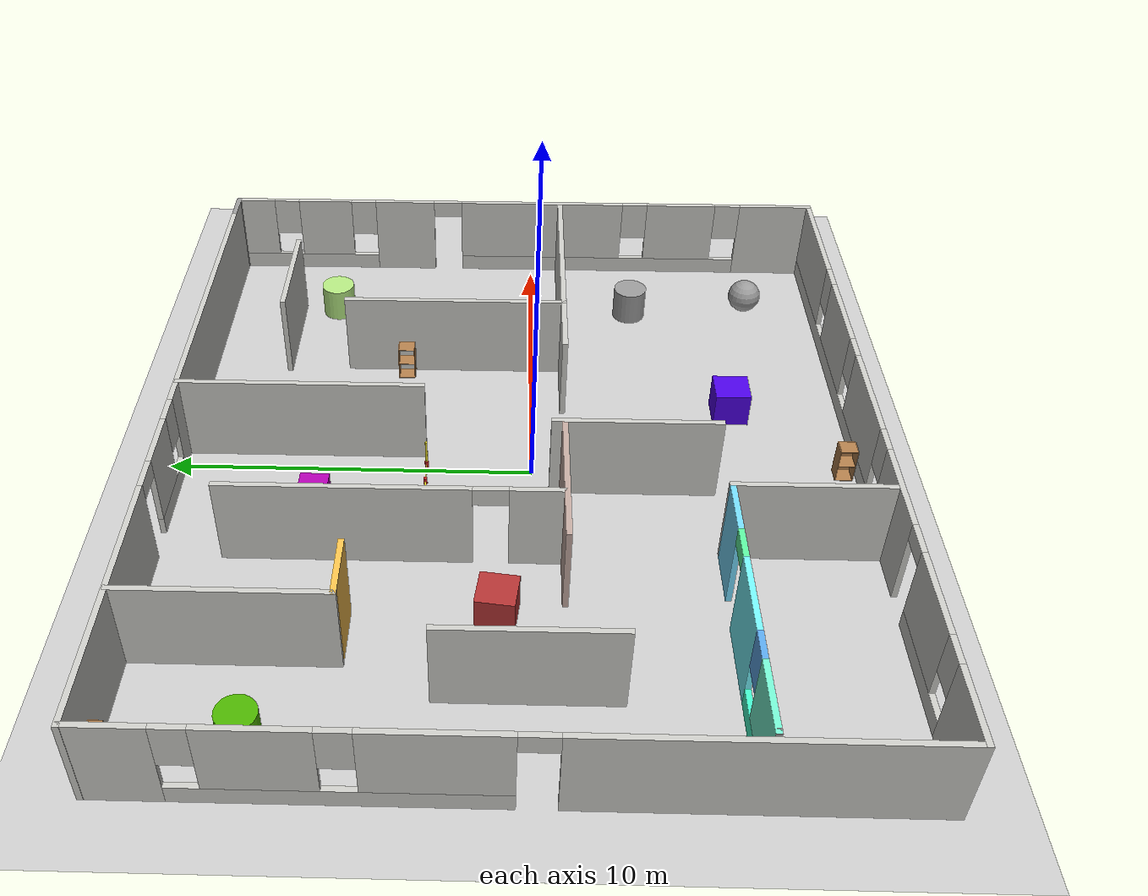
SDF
<sdf version="1.7">
 <world name="default">
  <light name="sun" type="directional">
   <pose>0 0 10 0 -0 0</pose>
   <diffuse>0.8 0.8 0.8 1</diffuse>
   <specular>0.2 0.2 0.2 1</specular>
   <attenuation>
    <range>1000</range>
    <constant>0.9</constant>
    <linear>0.01</linear>
    <quadratic>0.001</quadratic>
   </attenuation>
   <direction>-0.5 0.1 -0.9</direction>
   <spot><inner_angle>0</inner_angle><outer_angle>0</outer_angle><falloff>0</falloff></spot>
  </light>
  <model name="ground_plane">
   <static>1</static>
   <link name="link">
    <collision name="collision">
     <geometry><plane><normal>0 0 1</normal><size>100 100</size></plane></geometry>
     <surface><friction><ode><mu>100</mu><mu2>50</mu2></ode></friction></surface>
    </collision>
    <visual name="visual">
     <cast_shadows>0</cast_shadows>
     <geometry><plane><normal>0 0 1</normal><size>100 100</size></plane></geometry>
     <material>
      <script><uri>file://media/materials/scripts/gazebo.material</uri><name>Gazebo/Grey</name></script>
     </material>
    </visual>
   </link>
  </model>
  <gravity>0 0 -9.8</gravity>
  <magnetic_field>6e-06 2.3e-05 -4.2e-05</magnetic_field>
  <atmosphere type="adiabatic"/>
  <physics name="default_physics" default="0" type="ode">
   <max_step_size>0.001</max_step_size>
   <real_time_factor>1</real_time_factor>
   <real_time_update_rate>1000</real_time_update_rate>
  </physics>
  <scene><ambient>0.4 0.4 0.4 1</ambient><background>0.7 0.7 0.7 1</background><shadows>1</shadows></scene>
  <spherical_coordinates>
   <surface_model>EARTH_WGS84</surface_model>
   <latitude_deg>0</latitude_deg>
   <longitude_deg>0</longitude_deg>
   <elevation>0</elevation>
   <heading_deg>0</heading_deg>
  </spherical_coordinates>
  <model name="unit_cylinder">
   <pose>7.77748 -3.12633 0.499994 -3e-06 -1e-06 -0</pose>
   <link name="link">
    <inertial>
     <mass>1</mass>
     <inertia><ixx>0.145833</ixx><ixy>0</ixy><ixz>0</ixz><iyy>0.145833</iyy><iyz>0</iyz><izz>0.125</izz></inertia>
    </inertial>
    <collision name="collision">
     <geometry><cylinder><radius>0.5</radius><length>1</length></cylinder></geometry>
    </collision>
    <visual name="visual">
     <geometry><cylinder><radius>0.5</radius><length>1</length></cylinder></geometry>
     <material>
      <script><name>Gazebo/Grey</name><uri>file://media/materials/scripts/gazebo.material</uri></script>
     </material>
    </visual>
   </link>
  </model>
  <model name="unit_sphere">
   <pose>8.212 -6.8507 0.5 0 -0 0</pose>
   <link name="link">
    <inertial>
     <mass>1</mass>
     <inertia><ixx>0.1</ixx><ixy>0</ixy><ixz>0</ixz><iyy>0.1</iyy><iyz>0</iyz><izz>0.1</izz></inertia>
    </inertial>
    <collision name="collision"><geometry><sphere><radius>0.5</radius></sphere></geometry></collision>
    <visual name="visual">
     <geometry><sphere><radius>0.5</radius></sphere></geometry>
     <material>
      <script><name>Gazebo/Grey</name><uri>file://media/materials/scripts/gazebo.material</uri></script>
     </material>
    </visual>
   </link>
  </model>
  <model name="my_ball">
   <link name="link_0">
    <inertial>
     <mass>1</mass>
     <inertia><ixx>0.1</ixx><ixy>0</ixy><ixz>0</ixz><iyy>0.1</iyy><iyz>0</iyz><izz>0.1</izz></inertia>
    </inertial>
    <visual name="visual">
     <geometry><sphere><radius>0.1</radius></sphere></geometry>
     <material>
      <lighting>1</lighting>
      <script><uri>file://media/materials/scripts/gazebo.material</uri><name>Gazebo/White</name></script>
      <ambient>1 1 1 1</ambient>
      <diffuse>1 1 1 1</diffuse>
      <specular>1 1 1 1</specular>
      <emissive>1 1 1 1</emissive>
      <shader type="vertex"><normal_map>__default__</normal_map></shader>
     </material>
    </visual>
    <collision name="collision">
     <geometry><sphere><radius>0.1</radius></sphere></geometry>
     <surface>
      <friction>
       <ode><mu>1</mu><mu2>1</mu2><fdir1>0 0 0</fdir1><slip1>0</slip1><slip2>0</slip2></ode>
       <torsional>
        <coefficient>1</coefficient>
        <patch_radius>0</patch_radius>
        <surface_radius>0</surface_radius>
        <use_patch_radius>1</use_patch_radius>
        <ode><slip>0</slip></ode>
       </torsional>
      </friction>
      <bounce><restitution_coefficient>0</restitution_coefficient><threshold>1e+06</threshold></bounce>
      <contact>
       <collide_without_contact>0</collide_without_contact>
       <collide_without_contact_bitmask>1</collide_without_contact_bitmask>
       <collide_bitmask>1</collide_bitmask>
       <ode>
        <soft_cfm>0</soft_cfm>
        <soft_erp>0.2</soft_erp>
        <kp>1e+13</kp>
        <kd>1</kd>
        <max_vel>0.01</max_vel>
        <min_depth>0</min_depth>
       </ode>
       <bullet>
        <split_impulse>1</split_impulse>
        <split_impulse_penetration_threshold>-0.01</split_impulse_penetration_threshold>
        <soft_cfm>0</soft_cfm>
        <soft_erp>0.2</soft_erp>
        <kp>1e+13</kp>
        <kd>1</kd>
       </bullet>
      </contact>
     </surface>
    </collision>
   </link>
   <static>0</static>
   <pose>12.4706 -2.06062 0.1 0 -0 0</pose>
  </model>
  <model name="unit_box_1_0">
   <link name="link">
    <inertial>
     <mass>0.354011</mass>
     <inertia>
      <ixx>0.0472343</ixx>
      <ixy>0</ixy>
      <ixz>0</ixz>
      <iyy>0.0356513</iyy>
      <iyz>0</iyz>
      <izz>0.0238838</izz>
     </inertia>
    </inertial>
    <visual name="visual">
     <geometry><box><size>0.456597 0.775316 1</size></box></geometry>
     <material>
      <script><name>Gazebo/Grey</name><uri>file://media/materials/scripts/gazebo.material</uri></script>
      <shader type="pixel"><normal_map>__default__</normal_map></shader>
      <ambient>0.7 0 0.7 0</ambient>
      <diffuse>0.7 0.7 0.7 1</diffuse>
      <specular>0.01 0.01 0.01 1</specular>
      <emissive>0 0 0 1</emissive>
     </material>
    </visual>
    <collision name="collision">
     <geometry><box><size>0.456597 0.775316 1</size></box></geometry>
     <surface>
      <friction>
       <ode><mu>1</mu><mu2>1</mu2><fdir1>0 0 0</fdir1><slip1>0</slip1><slip2>0</slip2></ode>
       <torsional>
        <coefficient>1</coefficient>
        <patch_radius>0</patch_radius>
        <surface_radius>0</surface_radius>
        <use_patch_radius>1</use_patch_radius>
        <ode><slip>0</slip></ode>
       </torsional>
      </friction>
      <bounce><restitution_coefficient>0</restitution_coefficient><threshold>1e+06</threshold></bounce>
      <contact>
       <collide_without_contact>0</collide_without_contact>
       <collide_without_contact_bitmask>1</collide_without_contact_bitmask>
       <collide_bitmask>1</collide_bitmask>
       <ode>
        <soft_cfm>0</soft_cfm>
        <soft_erp>0.2</soft_erp>
        <kp>1e+13</kp>
        <kd>1</kd>
        <max_vel>0.01</max_vel>
        <min_depth>0</min_depth>
       </ode>
       <bullet>
        <split_impulse>1</split_impulse>
        <split_impulse_penetration_threshold>-0.01</split_impulse_penetration_threshold>
        <soft_cfm>0</soft_cfm>
        <soft_erp>0.2</soft_erp>
        <kp>1e+13</kp>
        <kd>1</kd>
       </bullet>
      </contact>
     </surface>
    </collision>
   </link>
   <static>0</static>
   <pose>-1.52355 5.76066 0.499996 9e-06 2e-06 -0.02596</pose>
  </model>
  <model name="unit_box12">
   <link name="link">
    <inertial>
     <mass>1</mass>
     <inertia>
      <ixx>0.166667</ixx>
      <ixy>0</ixy>
      <ixz>0</ixz>
      <iyy>0.166667</iyy>
      <iyz>0</iyz>
      <izz>0.166667</izz>
     </inertia>
    </inertial>
    <visual name="visual">
     <geometry><box><size>1 1 1</size></box></geometry>
     <material>
      <script><name>Gazebo/Grey</name><uri>file://media/materials/scripts/gazebo.material</uri></script>
      <shader type="pixel"><normal_map>__default__</normal_map></shader>
      <ambient>0.3 0 0.9 0</ambient>
      <diffuse>0.7 0.7 0.7 1</diffuse>
      <specular>0.01 0.01 0.01 1</specular>
      <emissive>0 0 0 1</emissive>
     </material>
    </visual>
    <collision name="collision">
     <geometry><box><size>1 1 1</size></box></geometry>
     <surface>
      <friction>
       <ode><mu>1</mu><mu2>1</mu2><fdir1>0 0 0</fdir1><slip1>0</slip1><slip2>0</slip2></ode>
       <torsional>
        <coefficient>1</coefficient>
        <patch_radius>0</patch_radius>
        <surface_radius>0</surface_radius>
        <use_patch_radius>1</use_patch_radius>
        <ode><slip>0</slip></ode>
       </torsional>
      </friction>
      <bounce><restitution_coefficient>0</restitution_coefficient><threshold>1e+06</threshold></bounce>
      <contact>
       <collide_without_contact>0</collide_without_contact>
       <collide_without_contact_bitmask>1</collide_without_contact_bitmask>
       <collide_bitmask>1</collide_bitmask>
       <ode>
        <soft_cfm>0</soft_cfm>
        <soft_erp>0.2</soft_erp>
        <kp>1e+13</kp>
        <kd>1</kd>
        <max_vel>0.01</max_vel>
        <min_depth>0</min_depth>
       </ode>
       <bullet>
        <split_impulse>1</split_impulse>
        <split_impulse_penetration_threshold>-0.01</split_impulse_penetration_threshold>
        <soft_cfm>0</soft_cfm>
        <soft_erp>0.2</soft_erp>
        <kp>1e+13</kp>
        <kd>1</kd>
       </bullet>
      </contact>
     </surface>
    </collision>
   </link>
   <static>0</static>
   <pose>2.74369 -5.72825 0.5 0 -0 0</pose>
  </model>
  <model name="unit_cylinder_13">
   <link name="link">
    <inertial>
     <mass>1</mass>
     <inertia><ixx>0.145833</ixx><ixy>0</ixy><ixz>0</ixz><iyy>0.145833</iyy><iyz>0</iyz><izz>0.125</izz></inertia>
    </inertial>
    <visual name="visual">
     <geometry><cylinder><radius>0.5</radius><length>1</length></cylinder></geometry>
     <material>
      <script><name>Gazebo/Grey</name><uri>file://media/materials/scripts/gazebo.material</uri></script>
      <shader type="pixel"><normal_map>__default__</normal_map></shader>
      <ambient>0.3 0.7 0 0</ambient>
      <diffuse>0.7 0.7 0.7 1</diffuse>
      <specular>0.01 0.01 0.01 1</specular>
      <emissive>0 0 0 1</emissive>
     </material>
    </visual>
    <collision name="collision">
     <geometry><cylinder><radius>0.5</radius><length>1</length></cylinder></geometry>
     <surface>
      <friction>
       <ode><mu>1</mu><mu2>1</mu2><fdir1>0 0 0</fdir1><slip1>0</slip1><slip2>0</slip2></ode>
       <torsional>
        <coefficient>1</coefficient>
        <patch_radius>0</patch_radius>
        <surface_radius>0</surface_radius>
        <use_patch_radius>1</use_patch_radius>
        <ode><slip>0</slip></ode>
       </torsional>
      </friction>
      <bounce><restitution_coefficient>0</restitution_coefficient><threshold>1e+06</threshold></bounce>
      <contact>
       <collide_without_contact>0</collide_without_contact>
       <collide_without_contact_bitmask>1</collide_without_contact_bitmask>
       <collide_bitmask>1</collide_bitmask>
       <ode>
        <soft_cfm>0</soft_cfm>
        <soft_erp>0.2</soft_erp>
        <kp>1e+13</kp>
        <kd>1</kd>
        <max_vel>0.01</max_vel>
        <min_depth>0</min_depth>
       </ode>
       <bullet>
        <split_impulse>1</split_impulse>
        <split_impulse_penetration_threshold>-0.01</split_impulse_penetration_threshold>
        <soft_cfm>0</soft_cfm>
        <soft_erp>0.2</soft_erp>
        <kp>1e+13</kp>
        <kd>1</kd>
       </bullet>
      </contact>
     </surface>
    </collision>
   </link>
   <static>0</static>
   <pose>-9.10904 6.48116 0.499998 3e-06 1e-06 -0</pose>
  </model>
  <model name="unit_box_15">
   <link name="link">
    <inertial>
     <mass>1</mass>
     <inertia>
      <ixx>0.166667</ixx>
      <ixy>0</ixy>
      <ixz>0</ixz>
      <iyy>0.166667</iyy>
      <iyz>0</iyz>
      <izz>0.166667</izz>
     </inertia>
    </inertial>
    <visual name="visual">
     <geometry><box><size>1 1 1</size></box></geometry>
     <material>
      <script><name>Gazebo/Grey</name><uri>file://media/materials/scripts/gazebo.material</uri></script>
      <shader type="pixel"><normal_map>__default__</normal_map></shader>
      <ambient>0.7 0.2 0.2 0</ambient>
      <diffuse>0.7 0.7 0.7 1</diffuse>
      <specular>0.01 0.01 0.01 1</specular>
      <emissive>0 0 0 1</emissive>
     </material>
    </visual>
    <collision name="collision">
     <geometry><box><size>1 1 1</size></box></geometry>
     <surface>
      <friction>
       <ode><mu>1</mu><mu2>1</mu2><fdir1>0 0 0</fdir1><slip1>0</slip1><slip2>0</slip2></ode>
       <torsional>
        <coefficient>1</coefficient>
        <patch_radius>0</patch_radius>
        <surface_radius>0</surface_radius>
        <use_patch_radius>1</use_patch_radius>
        <ode><slip>0</slip></ode>
       </torsional>
      </friction>
      <bounce><restitution_coefficient>0</restitution_coefficient><threshold>1e+06</threshold></bounce>
      <contact>
       <collide_without_contact>0</collide_without_contact>
       <collide_without_contact_bitmask>1</collide_without_contact_bitmask>
       <collide_bitmask>1</collide_bitmask>
       <ode>
        <soft_cfm>0</soft_cfm>
        <soft_erp>0.2</soft_erp>
        <kp>1e+13</kp>
        <kd>1</kd>
        <max_vel>0.01</max_vel>
        <min_depth>0</min_depth>
       </ode>
       <bullet>
        <split_impulse>1</split_impulse>
        <split_impulse_penetration_threshold>-0.01</split_impulse_penetration_threshold>
        <soft_cfm>0</soft_cfm>
        <soft_erp>0.2</soft_erp>
        <kp>1e+13</kp>
        <kd>1</kd>
       </bullet>
      </contact>
     </surface>
    </collision>
   </link>
   <static>0</static>
   <pose>-5.30929 0.86418 0.499999 1.5708 2e-06 -0.128436</pose>
  </model>
  <model name="simple_arm">
   <link name="arm_base">
    <inertial>
     <pose>0 0 0.00099 0 -0 0</pose>
     <inertia><ixx>1.11</ixx><ixy>0</ixy><ixz>0</ixz><iyy>100.11</iyy><iyz>0</iyz><izz>1.01</izz></inertia>
     <mass>101</mass>
    </inertial>
    <collision name="arm_base_geom">
     <pose>0 0 0.05 0 -0 0</pose>
     <geometry><box><size>1 1 0.1</size></box></geometry>
    </collision>
    <visual name="arm_base_geom_visual">
     <pose>0 0 0.05 0 -0 0</pose>
     <geometry><box><size>1 1 0.1</size></box></geometry>
     <material>
      <script><uri>file://media/materials/scripts/gazebo.material</uri><name>Gazebo/Blue</name></script>
     </material>
    </visual>
    <collision name="arm_base_geom_arm_trunk">
     <pose>0 0 0.6 0 -0 0</pose>
     <geometry><cylinder><radius>0.05</radius><length>1</length></cylinder></geometry>
    </collision>
    <visual name="arm_base_geom_arm_trunk_visual">
     <pose>0 0 0.6 0 -0 0</pose>
     <geometry><cylinder><radius>0.05</radius><length>1</length></cylinder></geometry>
     <material>
      <script><uri>file://media/materials/scripts/gazebo.material</uri><name>Gazebo/Red</name></script>
     </material>
    </visual>
   </link>
   <link name="arm_shoulder_pan">
    <pose>0 0 1.1 0 -0 0</pose>
    <inertial>
     <pose>0.045455 0 0 0 -0 0</pose>
     <inertia><ixx>0.011</ixx><ixy>0</ixy><ixz>0</ixz><iyy>0.0225</iyy><iyz>0</iyz><izz>0.0135</izz></inertia>
     <mass>1.1</mass>
    </inertial>
    <collision name="arm_shoulder_pan_geom">
     <pose>0 0 0.05 0 -0 0</pose>
     <geometry><cylinder><radius>0.05</radius><length>0.1</length></cylinder></geometry>
    </collision>
    <visual name="arm_shoulder_pan_geom_visual">
     <pose>0 0 0.05 0 -0 0</pose>
     <geometry><cylinder><radius>0.05</radius><length>0.1</length></cylinder></geometry>
     <material>
      <script><uri>file://media/materials/scripts/gazebo.material</uri><name>Gazebo/Yellow</name></script>
     </material>
    </visual>
    <collision name="arm_shoulder_pan_geom_arm_shoulder">
     <pose>0.55 0 0.05 0 -0 0</pose>
     <geometry><box><size>1 0.05 0.1</size></box></geometry>
    </collision>
    <visual name="arm_shoulder_pan_geom_arm_shoulder_visual">
     <pose>0.55 0 0.05 0 -0 0</pose>
     <geometry><box><size>1 0.05 0.1</size></box></geometry>
     <material>
      <script><uri>file://media/materials/scripts/gazebo.material</uri><name>Gazebo/Yellow</name></script>
     </material>
    </visual>
   </link>
   <link name="arm_elbow_pan">
    <pose>1.05 0 1.1 0 -0 0</pose>
    <inertial>
     <pose>0.0875 0 0.083333 0 -0 0</pose>
     <inertia>
      <ixx>0.031</ixx>
      <ixy>0</ixy>
      <ixz>0.005</ixz>
      <iyy>0.07275</iyy>
      <iyz>0</iyz>
      <izz>0.04475</izz>
     </inertia>
     <mass>1.2</mass>
    </inertial>
    <collision name="arm_elbow_pan_geom">
     <pose>0 0 0.1 0 -0 0</pose>
     <geometry><cylinder><radius>0.05</radius><length>0.2</length></cylinder></geometry>
    </collision>
    <visual name="arm_elbow_pan_geom_visual">
     <pose>0 0 0.1 0 -0 0</pose>
     <geometry><cylinder><radius>0.05</radius><length>0.2</length></cylinder></geometry>
     <material>
      <script><uri>file://media/materials/scripts/gazebo.material</uri><name>Gazebo/Red</name></script>
     </material>
    </visual>
    <collision name="arm_elbow_pan_geom_arm_elbow">
     <pose>0.3 0 0.15 0 -0 0</pose>
     <geometry><box><size>0.5 0.03 0.1</size></box></geometry>
    </collision>
    <visual name="arm_elbow_pan_geom_arm_elbow_visual">
     <pose>0.3 0 0.15 0 -0 0</pose>
     <geometry><box><size>0.5 0.03 0.1</size></box></geometry>
     <material>
      <script><uri>file://media/materials/scripts/gazebo.material</uri><name>Gazebo/Yellow</name></script>
     </material>
    </visual>
    <collision name="arm_elbow_pan_geom_arm_wrist">
     <pose>0.55 0 0.15 0 -0 0</pose>
     <geometry><cylinder><radius>0.05</radius><length>0.3</length></cylinder></geometry>
    </collision>
    <visual name="arm_elbow_pan_geom_arm_wrist_visual">
     <pose>0.55 0 0.15 0 -0 0</pose>
     <geometry><cylinder><radius>0.05</radius><length>0.3</length></cylinder></geometry>
     <material>
      <script><uri>file://media/materials/scripts/gazebo.material</uri><name>Gazebo/Red</name></script>
     </material>
    </visual>
   </link>
   <link name="arm_wrist_lift">
    <pose>1.6 0 1.05 0 -0 0</pose>
    <inertial>
     <inertia><ixx>0.01</ixx><ixy>0</ixy><ixz>0</ixz><iyy>0.01</iyy><iyz>0</iyz><izz>0.001</izz></inertia>
     <mass>0.1</mass>
    </inertial>
    <collision name="arm_wrist_lift_geom">
     <pose>0 0 0.5 0 -0 0</pose>
     <geometry><cylinder><radius>0.03</radius><length>1</length></cylinder></geometry>
    </collision>
    <visual name="arm_wrist_lift_geom_visual">
     <pose>0 0 0.5 0 -0 0</pose>
     <geometry><cylinder><radius>0.03</radius><length>1</length></cylinder></geometry>
     <material>
      <script><uri>file://media/materials/scripts/gazebo.material</uri><name>Gazebo/Yellow</name></script>
     </material>
    </visual>
   </link>
   <link name="arm_wrist_roll">
    <pose>1.6 0 1 0 -0 0</pose>
    <inertial>
     <inertia><ixx>0.01</ixx><ixy>0</ixy><ixz>0</ixz><iyy>0.01</iyy><iyz>0</iyz><izz>0.001</izz></inertia>
     <mass>0.1</mass>
    </inertial>
    <collision name="arm_wrist_roll_geom">
     <pose>0 0 0.025 0 -0 0</pose>
     <geometry><cylinder><radius>0.05</radius><length>0.05</length></cylinder></geometry>
    </collision>
    <visual name="arm_wrist_roll_geom_visual">
     <pose>0 0 0.025 0 -0 0</pose>
     <geometry><cylinder><radius>0.05</radius><length>0.05</length></cylinder></geometry>
     <material>
      <script><uri>file://media/materials/scripts/gazebo.material</uri><name>Gazebo/Red</name></script>
     </material>
    </visual>
   </link>
   <joint name="arm_shoulder_pan_joint" type="revolute">
    <parent>arm_base</parent>
    <child>arm_shoulder_pan</child>
    <axis>
     <dynamics>
      <damping>1</damping>
      <friction>0</friction>
      <spring_reference>0</spring_reference>
      <spring_stiffness>0</spring_stiffness>
     </dynamics>
     <xyz expressed_in="__model__">0 0 1</xyz>
     <limit><lower>-1e+16</lower><upper>1e+16</upper></limit>
    </axis>
   </joint>
   <joint name="arm_elbow_pan_joint" type="revolute">
    <parent>arm_shoulder_pan</parent>
    <child>arm_elbow_pan</child>
    <axis>
     <dynamics>
      <damping>1</damping>
      <friction>0</friction>
      <spring_reference>0</spring_reference>
      <spring_stiffness>0</spring_stiffness>
     </dynamics>
     <xyz expressed_in="__model__">0 0 1</xyz>
     <limit><lower>-1e+16</lower><upper>1e+16</upper></limit>
    </axis>
   </joint>
   <joint name="arm_wrist_lift_joint" type="prismatic">
    <parent>arm_elbow_pan</parent>
    <child>arm_wrist_lift</child>
    <axis>
     <dynamics>
      <damping>1</damping>
      <friction>0</friction>
      <spring_reference>0</spring_reference>
      <spring_stiffness>0</spring_stiffness>
     </dynamics>
     <limit><lower>-0.8</lower><upper>0.1</upper></limit>
     <xyz expressed_in="__model__">0 0 1</xyz>
    </axis>
   </joint>
   <joint name="arm_wrist_roll_joint" type="revolute">
    <parent>arm_wrist_lift</parent>
    <child>arm_wrist_roll</child>
    <axis>
     <dynamics>
      <damping>1</damping>
      <friction>0</friction>
      <spring_reference>0</spring_reference>
      <spring_stiffness>0</spring_stiffness>
     </dynamics>
     <limit><lower>-2.99999</lower><upper>2.99999</upper></limit>
     <xyz expressed_in="__model__">0 0 1</xyz>
    </axis>
   </joint>
   <pose>-2.79115 2.80103 -0 0 -0 -0.006956</pose>
  </model>
  <model name="cabinet">
   <static>1</static>
   <link name="cabinet_bottom_plate">
    <inertial>
     <pose>0 0 -1 0 -0 0</pose>
     <inertia><ixx>2.05</ixx><ixy>0</ixy><ixz>0</ixz><iyy>2.05</iyy><iyz>0</iyz><izz>2.05</izz></inertia>
     <mass>25</mass>
    </inertial>
    <collision name="cabinet_bottom_plate_geom">
     <pose>0 0 0.01 0 -0 0</pose>
     <geometry><box><size>0.45 0.45 0.02</size></box></geometry>
    </collision>
    <visual name="cabinet_bottom_plate_geom_visual">
     <pose>0 0 0.01 0 -0 0</pose>
     <geometry><box><size>0.45 0.45 0.02</size></box></geometry>
     <material>
      <script><uri>file://media/materials/scripts/gazebo.material</uri><name>Gazebo/Wood</name></script>
     </material>
    </visual>
    <collision name="cabinet_bottom_plate_geom_cabinet_back_plate">
     <pose>0.235 0 0.51 0 -0 0</pose>
     <geometry><box><size>0.02 0.45 1.02</size></box></geometry>
    </collision>
    <visual name="cabinet_bottom_plate_geom_cabinet_back_plate_visual">
     <pose>0.235 0 0.51 0 -0 0</pose>
     <geometry><box><size>0.02 0.45 1.02</size></box></geometry>
     <material>
      <script><uri>file://media/materials/scripts/gazebo.material</uri><name>Gazebo/Wood</name></script>
     </material>
    </visual>
    <collision name="cabinet_bottom_plate_geom_cabinet_left_plate">
     <pose>0 0.235 0.51 0 -0 0</pose>
     <geometry><box><size>0.45 0.02 1.02</size></box></geometry>
    </collision>
    <visual name="cabinet_bottom_plate_geom_cabinet_left_plate_visual">
     <pose>0 0.235 0.51 0 -0 0</pose>
     <geometry><box><size>0.45 0.02 1.02</size></box></geometry>
     <material>
      <script><uri>file://media/materials/scripts/gazebo.material</uri><name>Gazebo/Wood</name></script>
     </material>
    </visual>
    <collision name="cabinet_bottom_plate_geom_cabinet_middle_plate">
     <pose>0 0 0.51 0 -0 0</pose>
     <geometry><box><size>0.45 0.45 0.02</size></box></geometry>
    </collision>
    <visual name="cabinet_bottom_plate_geom_cabinet_middle_plate_visual">
     <pose>0 0 0.51 0 -0 0</pose>
     <geometry><box><size>0.45 0.45 0.02</size></box></geometry>
     <material>
      <script><uri>file://media/materials/scripts/gazebo.material</uri><name>Gazebo/Wood</name></script>
     </material>
    </visual>
    <collision name="cabinet_bottom_plate_geom_cabinet_right_plate">
     <pose>0 -0.235 0.51 0 -0 0</pose>
     <geometry><box><size>0.45 0.02 1.02</size></box></geometry>
    </collision>
    <visual name="cabinet_bottom_plate_geom_cabinet_right_plate_visual">
     <pose>0 -0.235 0.51 0 -0 0</pose>
     <geometry><box><size>0.45 0.02 1.02</size></box></geometry>
     <material>
      <script><uri>file://media/materials/scripts/gazebo.material</uri><name>Gazebo/Wood</name></script>
     </material>
    </visual>
    <collision name="cabinet_bottom_plate_geom_cabinet_top_plate">
     <pose>0 0 1.01 0 -0 0</pose>
     <geometry><box><size>0.45 0.45 0.02</size></box></geometry>
    </collision>
    <visual name="cabinet_bottom_plate_geom_cabinet_top_plate_visual">
     <pose>0 0 1.01 0 -0 0</pose>
     <geometry><box><size>0.45 0.45 0.02</size></box></geometry>
     <material>
      <script><uri>file://media/materials/scripts/gazebo.material</uri><name>Gazebo/Wood</name></script>
     </material>
    </visual>
   </link>
   <pose>4.44424 3.74258 0 0 -0 0</pose>
  </model>
  <model name="bookshelf">
   <static>1</static>
   <link name="link">
    <inertial><mass>1</mass></inertial>
    <collision name="back">
     <pose>0 0.005 0.6 0 -0 0</pose>
     <geometry><box><size>0.9 0.01 1.2</size></box></geometry>
    </collision>
    <visual name="visual1">
     <pose>0 0.005 0.6 0 -0 0</pose>
     <geometry><box><size>0.9 0.01 1.2</size></box></geometry>
     <material>
      <script><uri>file://media/materials/scripts/gazebo.material</uri><name>Gazebo/Wood</name></script>
     </material>
    </visual>
    <collision name="left_side">
     <pose>0.45 -0.195 0.6 0 -0 0</pose>
     <geometry><box><size>0.02 0.4 1.2</size></box></geometry>
    </collision>
    <visual name="visual2">
     <pose>0.45 -0.195 0.6 0 -0 0</pose>
     <geometry><box><size>0.02 0.4 1.2</size></box></geometry>
     <material>
      <script><uri>file://media/materials/scripts/gazebo.material</uri><name>Gazebo/Wood</name></script>
     </material>
    </visual>
    <collision name="right_side">
     <pose>-0.45 -0.195 0.6 0 -0 0</pose>
     <geometry><box><size>0.02 0.4 1.2</size></box></geometry>
    </collision>
    <visual name="visual3">
     <pose>-0.45 -0.195 0.6 0 -0 0</pose>
     <geometry><box><size>0.02 0.4 1.2</size></box></geometry>
     <material>
      <script><uri>file://media/materials/scripts/gazebo.material</uri><name>Gazebo/Wood</name></script>
     </material>
    </visual>
    <collision name="bottom">
     <pose>0 -0.195 0.03 0 -0 0</pose>
     <geometry><box><size>0.88 0.4 0.06</size></box></geometry>
    </collision>
    <visual name="visual4">
     <pose>0 -0.195 0.03 0 -0 0</pose>
     <geometry><box><size>0.88 0.4 0.06</size></box></geometry>
     <material>
      <script><uri>file://media/materials/scripts/gazebo.material</uri><name>Gazebo/Wood</name></script>
     </material>
    </visual>
    <collision name="top">
     <pose>0 -0.195 1.19 0 -0 0</pose>
     <geometry><box><size>0.88 0.4 0.02</size></box></geometry>
    </collision>
    <visual name="visual5">
     <pose>0 -0.195 1.19 0 -0 0</pose>
     <geometry><box><size>0.88 0.4 0.02</size></box></geometry>
     <material>
      <script><uri>file://media/materials/scripts/gazebo.material</uri><name>Gazebo/Wood</name></script>
     </material>
    </visual>
    <collision name="low_shelf">
     <pose>0 -0.195 0.43 0 -0 0</pose>
     <geometry><box><size>0.88 0.4 0.02</size></box></geometry>
    </collision>
    <visual name="visual6">
     <pose>0 -0.195 0.43 0 -0 0</pose>
     <geometry><box><size>0.88 0.4 0.02</size></box></geometry>
     <material>
      <script><uri>file://media/materials/scripts/gazebo.material</uri><name>Gazebo/Wood</name></script>
     </material>
    </visual>
    <collision name="high_shelf">
     <pose>0 -0.195 0.8 0 -0 0</pose>
     <geometry><box><size>0.88 0.4 0.02</size></box></geometry>
    </collision>
    <visual name="visual7">
     <pose>0 -0.195 0.8 0 -0 0</pose>
     <geometry><box><size>0.88 0.4 0.02</size></box></geometry>
     <material>
      <script><uri>file://media/materials/scripts/gazebo.material</uri><name>Gazebo/Wood</name></script>
     </material>
    </visual>
   </link>
   <pose>-10.0015 9.61111 0 0 -0 0</pose>
  </model>
  <model name="unit_box9">
   <link name="link">
    <inertial>
     <mass>1</mass>
     <inertia>
      <ixx>0.166667</ixx>
      <ixy>0</ixy>
      <ixz>0</ixz>
      <iyy>0.166667</iyy>
      <iyz>0</iyz>
      <izz>0.166667</izz>
     </inertia>
    </inertial>
    <visual name="visual">
     <geometry><box><size>1 1 1</size></box></geometry>
     <material>
      <script><name>Gazebo/Grey</name><uri>file://media/materials/scripts/gazebo.material</uri></script>
      <shader type="pixel"><normal_map>__default__</normal_map></shader>
      <ambient>0.4 0.5 0.8 0</ambient>
      <diffuse>0.7 0.7 0.7 1</diffuse>
      <specular>0.01 0.01 0.01 1</specular>
      <emissive>0 0 0 1</emissive>
     </material>
    </visual>
    <collision name="collision">
     <geometry><box><size>1 1 1</size></box></geometry>
     <surface>
      <friction>
       <ode><mu>1</mu><mu2>1</mu2><fdir1>0 0 0</fdir1><slip1>0</slip1><slip2>0</slip2></ode>
       <torsional>
        <coefficient>1</coefficient>
        <patch_radius>0</patch_radius>
        <surface_radius>0</surface_radius>
        <use_patch_radius>1</use_patch_radius>
        <ode><slip>0</slip></ode>
       </torsional>
      </friction>
      <bounce><restitution_coefficient>0</restitution_coefficient><threshold>1e+06</threshold></bounce>
      <contact>
       <collide_without_contact>0</collide_without_contact>
       <collide_without_contact_bitmask>1</collide_without_contact_bitmask>
       <collide_bitmask>1</collide_bitmask>
       <ode>
        <soft_cfm>0</soft_cfm>
        <soft_erp>0.2</soft_erp>
        <kp>1e+13</kp>
        <kd>1</kd>
        <max_vel>0.01</max_vel>
        <min_depth>0</min_depth>
       </ode>
       <bullet>
        <split_impulse>1</split_impulse>
        <split_impulse_penetration_threshold>-0.01</split_impulse_penetration_threshold>
        <soft_cfm>0</soft_cfm>
        <soft_erp>0.2</soft_erp>
        <kp>1e+13</kp>
        <kd>1</kd>
       </bullet>
      </contact>
     </surface>
    </collision>
   </link>
   <static>0</static>
   <pose>-10.066 -3.39499 0.5 0 0 -5e-06</pose>
  </model>
  <model name="unit_box90">
   <link name="link">
    <inertial>
     <mass>1</mass>
     <inertia>
      <ixx>0.166667</ixx>
      <ixy>0</ixy>
      <ixz>0</ixz>
      <iyy>0.166667</iyy>
      <iyz>0</iyz>
      <izz>0.166667</izz>
     </inertia>
    </inertial>
    <visual name="visual">
     <geometry><box><size>0.424568 2.43542 1</size></box></geometry>
     <material>
      <script><name>Gazebo/Grey</name><uri>file://media/materials/scripts/gazebo.material</uri></script>
      <shader type="pixel"><normal_map>__default__</normal_map></shader>
      <ambient>0.4 0.7 0.5 0</ambient>
      <diffuse>0.7 0.7 0.7 1</diffuse>
      <specular>0.01 0.01 0.01 1</specular>
      <emissive>0 0 0 1</emissive>
     </material>
    </visual>
    <collision name="collision">
     <geometry><box><size>0.424568 2.43542 1</size></box></geometry>
     <surface>
      <friction>
       <ode><mu>1</mu><mu2>1</mu2><fdir1>0 0 0</fdir1><slip1>0</slip1><slip2>0</slip2></ode>
       <torsional>
        <coefficient>1</coefficient>
        <patch_radius>0</patch_radius>
        <surface_radius>0</surface_radius>
        <use_patch_radius>1</use_patch_radius>
        <ode><slip>0</slip></ode>
       </torsional>
      </friction>
      <bounce><restitution_coefficient>0</restitution_coefficient><threshold>1e+06</threshold></bounce>
      <contact>
       <collide_without_contact>0</collide_without_contact>
       <collide_without_contact_bitmask>1</collide_without_contact_bitmask>
       <collide_bitmask>1</collide_bitmask>
       <ode>
        <soft_cfm>0</soft_cfm>
        <soft_erp>0.2</soft_erp>
        <kp>1e+13</kp>
        <kd>1</kd>
        <max_vel>0.01</max_vel>
        <min_depth>0</min_depth>
       </ode>
       <bullet>
        <split_impulse>1</split_impulse>
        <split_impulse_penetration_threshold>-0.01</split_impulse_penetration_threshold>
        <soft_cfm>0</soft_cfm>
        <soft_erp>0.2</soft_erp>
        <kp>1e+13</kp>
        <kd>1</kd>
       </bullet>
      </contact>
     </surface>
    </collision>
   </link>
   <static>0</static>
   <pose>-10.3425 2.41052 0.499946 -4.4e-05 -0 0.001559</pose>
  </model>
  <model name="cabinet_0">
   <static>1</static>
   <link name="cabinet_bottom_plate">
    <inertial>
     <pose>0 0 -1 0 -0 0</pose>
     <inertia><ixx>2.05</ixx><ixy>0</ixy><ixz>0</ixz><iyy>2.05</iyy><iyz>0</iyz><izz>2.05</izz></inertia>
     <mass>25</mass>
    </inertial>
    <collision name="cabinet_bottom_plate_geom">
     <pose>0 0 0.01 0 -0 0</pose>
     <geometry><box><size>0.45 0.45 0.02</size></box></geometry>
    </collision>
    <visual name="cabinet_bottom_plate_geom_visual">
     <pose>0 0 0.01 0 -0 0</pose>
     <geometry><box><size>0.45 0.45 0.02</size></box></geometry>
     <material>
      <script><uri>file://media/materials/scripts/gazebo.material</uri><name>Gazebo/Wood</name></script>
     </material>
    </visual>
    <collision name="cabinet_bottom_plate_geom_cabinet_back_plate">
     <pose>0.235 0 0.51 0 -0 0</pose>
     <geometry><box><size>0.02 0.45 1.02</size></box></geometry>
    </collision>
    <visual name="cabinet_bottom_plate_geom_cabinet_back_plate_visual">
     <pose>0.235 0 0.51 0 -0 0</pose>
     <geometry><box><size>0.02 0.45 1.02</size></box></geometry>
     <material>
      <script><uri>file://media/materials/scripts/gazebo.material</uri><name>Gazebo/Wood</name></script>
     </material>
    </visual>
    <collision name="cabinet_bottom_plate_geom_cabinet_left_plate">
     <pose>0 0.235 0.51 0 -0 0</pose>
     <geometry><box><size>0.45 0.02 1.02</size></box></geometry>
    </collision>
    <visual name="cabinet_bottom_plate_geom_cabinet_left_plate_visual">
     <pose>0 0.235 0.51 0 -0 0</pose>
     <geometry><box><size>0.45 0.02 1.02</size></box></geometry>
     <material>
      <script><uri>file://media/materials/scripts/gazebo.material</uri><name>Gazebo/Wood</name></script>
     </material>
    </visual>
    <collision name="cabinet_bottom_plate_geom_cabinet_middle_plate">
     <pose>0 0 0.51 0 -0 0</pose>
     <geometry><box><size>0.45 0.45 0.02</size></box></geometry>
    </collision>
    <visual name="cabinet_bottom_plate_geom_cabinet_middle_plate_visual">
     <pose>0 0 0.51 0 -0 0</pose>
     <geometry><box><size>0.45 0.45 0.02</size></box></geometry>
     <material>
      <script><uri>file://media/materials/scripts/gazebo.material</uri><name>Gazebo/Wood</name></script>
     </material>
    </visual>
    <collision name="cabinet_bottom_plate_geom_cabinet_right_plate">
     <pose>0 -0.235 0.51 0 -0 0</pose>
     <geometry><box><size>0.45 0.02 1.02</size></box></geometry>
    </collision>
    <visual name="cabinet_bottom_plate_geom_cabinet_right_plate_visual">
     <pose>0 -0.235 0.51 0 -0 0</pose>
     <geometry><box><size>0.45 0.02 1.02</size></box></geometry>
     <material>
      <script><uri>file://media/materials/scripts/gazebo.material</uri><name>Gazebo/Wood</name></script>
     </material>
    </visual>
    <collision name="cabinet_bottom_plate_geom_cabinet_top_plate">
     <pose>0 0 1.01 0 -0 0</pose>
     <geometry><box><size>0.45 0.45 0.02</size></box></geometry>
    </collision>
    <visual name="cabinet_bottom_plate_geom_cabinet_top_plate_visual">
     <pose>0 0 1.01 0 -0 0</pose>
     <geometry><box><size>0.45 0.45 0.02</size></box></geometry>
     <material>
      <script><uri>file://media/materials/scripts/gazebo.material</uri><name>Gazebo/Wood</name></script>
     </material>
    </visual>
   </link>
   <pose>0.120833 -8.54479 0 0 -0 0</pose>
  </model>
  <model name="ball_bearing">
   <link name="link">
    <pose>0 0 0.003 0 -0 0</pose>
    <inertial>
     <mass>0.0011</mass>
     <inertia>
      <ixx>3.96e-09</ixx>
      <ixy>0</ixy>
      <ixz>0</ixz>
      <iyy>3.96e-09</iyy>
      <iyz>0</iyz>
      <izz>3.96e-09</izz>
     </inertia>
    </inertial>
    <collision name="collision">
     <geometry><sphere><radius>0.003</radius></sphere></geometry>
     <surface>
      <contact>
       <poissons_ratio>0.305</poissons_ratio>
       <elastic_modulus>2e+11</elastic_modulus>
       <ode><kp>100000</kp><kd>100</kd><max_vel>100</max_vel><min_depth>0.001</min_depth></ode>
      </contact>
      <friction>
       <torsional>
        <coefficient>1</coefficient>
        <use_patch_radius>0</use_patch_radius>
        <surface_radius>0.01</surface_radius>
       </torsional>
      </friction>
     </surface>
    </collision>
    <visual name="visual">
     <geometry><sphere><radius>0.003</radius></sphere></geometry>
     <material>
      <script><uri>file://media/materials/scripts/gazebo.material</uri><name>Gazebo/Grey</name></script>
     </material>
    </visual>
    <velocity_decay><linear>0</linear><angular>0.005</angular></velocity_decay>
   </link>
   <pose>-4.13788 -6.77252 -0.001 0 -0 0</pose>
  </model>
  <model name="unit_cylinder_33">
   <link name="link">
    <inertial>
     <mass>1</mass>
     <inertia><ixx>0.145833</ixx><ixy>0</ixy><ixz>0</ixz><iyy>0.145833</iyy><iyz>0</iyz><izz>0.125</izz></inertia>
    </inertial>
    <visual name="visual">
     <geometry><cylinder><radius>0.5</radius><length>1</length></cylinder></geometry>
     <material>
      <script><name>Gazebo/Grey</name><uri>file://media/materials/scripts/gazebo.material</uri></script>
      <shader type="pixel"><normal_map>__default__</normal_map></shader>
      <ambient>0.7 0.9 0.5 0</ambient>
      <diffuse>0.7 0.7 0.7 1</diffuse>
      <specular>0.01 0.01 0.01 1</specular>
      <emissive>0 0 0 1</emissive>
     </material>
    </visual>
    <collision name="collision">
     <geometry><cylinder><radius>0.5</radius><length>1</length></cylinder></geometry>
     <surface>
      <friction>
       <ode><mu>1</mu><mu2>1</mu2><fdir1>0 0 0</fdir1><slip1>0</slip1><slip2>0</slip2></ode>
       <torsional>
        <coefficient>1</coefficient>
        <patch_radius>0</patch_radius>
        <surface_radius>0</surface_radius>
        <use_patch_radius>1</use_patch_radius>
        <ode><slip>0</slip></ode>
       </torsional>
      </friction>
      <bounce><restitution_coefficient>0</restitution_coefficient><threshold>1e+06</threshold></bounce>
      <contact>
       <collide_without_contact>0</collide_without_contact>
       <collide_without_contact_bitmask>1</collide_without_contact_bitmask>
       <collide_bitmask>1</collide_bitmask>
       <ode>
        <soft_cfm>0</soft_cfm>
        <soft_erp>0.2</soft_erp>
        <kp>1e+13</kp>
        <kd>1</kd>
        <max_vel>0.01</max_vel>
        <min_depth>0</min_depth>
       </ode>
       <bullet>
        <split_impulse>1</split_impulse>
        <split_impulse_penetration_threshold>-0.01</split_impulse_penetration_threshold>
        <soft_cfm>0</soft_cfm>
        <soft_erp>0.2</soft_erp>
        <kp>1e+13</kp>
        <kd>1</kd>
       </bullet>
      </contact>
     </surface>
    </collision>
   </link>
   <static>0</static>
   <pose>7.74534 6.17381 0.499998 3e-06 1e-06 -0</pose>
  </model>
  <model name="unit_box12_0">
   <link name="link">
    <inertial>
     <mass>1</mass>
     <inertia>
      <ixx>0.166667</ixx>
      <ixy>0</ixy>
      <ixz>0</ixz>
      <iyy>0.166667</iyy>
      <iyz>0</iyz>
      <izz>0.166667</izz>
     </inertia>
    </inertial>
    <visual name="visual">
     <geometry><box><size>1 1 1</size></box></geometry>
     <material>
      <script><name>Gazebo/Grey</name><uri>file://media/materials/scripts/gazebo.material</uri></script>
      <shader type="pixel"><normal_map>__default__</normal_map></shader>
      <ambient>0.5 0.3 1 0</ambient>
      <diffuse>0.7 0.7 0.7 1</diffuse>
      <specular>0.01 0.01 0.01 1</specular>
      <emissive>0 0 0 1</emissive>
     </material>
    </visual>
    <collision name="collision">
     <geometry><box><size>1 1 1</size></box></geometry>
     <surface>
      <friction>
       <ode><mu>1</mu><mu2>1</mu2><fdir1>0 0 0</fdir1><slip1>0</slip1><slip2>0</slip2></ode>
       <torsional>
        <coefficient>1</coefficient>
        <patch_radius>0</patch_radius>
        <surface_radius>0</surface_radius>
        <use_patch_radius>1</use_patch_radius>
        <ode><slip>0</slip></ode>
       </torsional>
      </friction>
      <bounce><restitution_coefficient>0</restitution_coefficient><threshold>1e+06</threshold></bounce>
      <contact>
       <collide_without_contact>0</collide_without_contact>
       <collide_without_contact_bitmask>1</collide_without_contact_bitmask>
       <collide_bitmask>1</collide_bitmask>
       <ode>
        <soft_cfm>0</soft_cfm>
        <soft_erp>0.2</soft_erp>
        <kp>1e+13</kp>
        <kd>1</kd>
        <max_vel>0.01</max_vel>
        <min_depth>0</min_depth>
       </ode>
       <bullet>
        <split_impulse>1</split_impulse>
        <split_impulse_penetration_threshold>-0.01</split_impulse_penetration_threshold>
        <soft_cfm>0</soft_cfm>
        <soft_erp>0.2</soft_erp>
        <kp>1e+13</kp>
        <kd>1</kd>
       </bullet>
      </contact>
     </surface>
    </collision>
   </link>
   <static>0</static>
   <pose>5.32386 2.44658 0.5 0 -0 5e-06</pose>
  </model>
  <model name="unit_box14">
   <link name="link">
    <inertial>
     <mass>1</mass>
     <inertia>
      <ixx>0.166667</ixx>
      <ixy>0</ixy>
      <ixz>0</ixz>
      <iyy>0.166667</iyy>
      <iyz>0</iyz>
      <izz>0.166667</izz>
     </inertia>
    </inertial>
    <visual name="visual">
     <geometry><box><size>0.369721 0.645498 1</size></box></geometry>
     <material>
      <script><name>Gazebo/Grey</name><uri>file://media/materials/scripts/gazebo.material</uri></script>
      <shader type="pixel"><normal_map>__default__</normal_map></shader>
      <ambient>0.4 0.4 0.2 0</ambient>
      <diffuse>0.7 0.7 0.7 1</diffuse>
      <specular>0.01 0.01 0.01 1</specular>
      <emissive>0 0 0 1</emissive>
     </material>
    </visual>
    <collision name="collision">
     <geometry><box><size>0.369721 0.645498 1</size></box></geometry>
     <surface>
      <friction>
       <ode><mu>1</mu><mu2>1</mu2><fdir1>0 0 0</fdir1><slip1>0</slip1><slip2>0</slip2></ode>
       <torsional>
        <coefficient>1</coefficient>
        <patch_radius>0</patch_radius>
        <surface_radius>0</surface_radius>
        <use_patch_radius>1</use_patch_radius>
        <ode><slip>0</slip></ode>
       </torsional>
      </friction>
      <bounce><restitution_coefficient>0</restitution_coefficient><threshold>1e+06</threshold></bounce>
      <contact>
       <collide_without_contact>0</collide_without_contact>
       <collide_without_contact_bitmask>1</collide_without_contact_bitmask>
       <collide_bitmask>1</collide_bitmask>
       <ode>
        <soft_cfm>0</soft_cfm>
        <soft_erp>0.2</soft_erp>
        <kp>1e+13</kp>
        <kd>1</kd>
        <max_vel>0.01</max_vel>
        <min_depth>0</min_depth>
       </ode>
       <bullet>
        <split_impulse>1</split_impulse>
        <split_impulse_penetration_threshold>-0.01</split_impulse_penetration_threshold>
        <soft_cfm>0</soft_cfm>
        <soft_erp>0.2</soft_erp>
        <kp>1e+13</kp>
        <kd>1</kd>
       </bullet>
      </contact>
     </surface>
    </collision>
   </link>
   <static>0</static>
   <pose>-10.3777 -1.60096 0.5 0 -0 5e-06</pose>
  </model>
  <model name="unit_box_green">
   <link name="link">
    <inertial>
     <mass>1</mass>
     <inertia>
      <ixx>0.166667</ixx>
      <ixy>0</ixy>
      <ixz>0</ixz>
      <iyy>0.166667</iyy>
      <iyz>0</iyz>
      <izz>0.166667</izz>
     </inertia>
    </inertial>
    <visual name="visual">
     <geometry><box><size>0.617794 0.479075 1</size></box></geometry>
     <material>
      <script><name>Gazebo/Grey</name><uri>file://media/materials/scripts/gazebo.material</uri></script>
      <shader type="pixel"><normal_map>__default__</normal_map></shader>
      <ambient>0.2 1 0.3 0</ambient>
      <diffuse>0.7 0.7 0.7 1</diffuse>
      <specular>0.01 0.01 0.01 1</specular>
      <emissive>0 0 0 1</emissive>
     </material>
    </visual>
    <collision name="collision">
     <geometry><box><size>0.617794 0.479075 1</size></box></geometry>
     <surface>
      <friction>
       <ode><mu>1</mu><mu2>1</mu2><fdir1>0 0 0</fdir1><slip1>0</slip1><slip2>0</slip2></ode>
       <torsional>
        <coefficient>1</coefficient>
        <patch_radius>0</patch_radius>
        <surface_radius>0</surface_radius>
        <use_patch_radius>1</use_patch_radius>
        <ode><slip>0</slip></ode>
       </torsional>
      </friction>
      <bounce><restitution_coefficient>0</restitution_coefficient><threshold>1e+06</threshold></bounce>
      <contact>
       <collide_without_contact>0</collide_without_contact>
       <collide_without_contact_bitmask>1</collide_without_contact_bitmask>
       <collide_bitmask>1</collide_bitmask>
       <ode>
        <soft_cfm>0</soft_cfm>
        <soft_erp>0.2</soft_erp>
        <kp>1e+13</kp>
        <kd>1</kd>
        <max_vel>0.01</max_vel>
        <min_depth>0</min_depth>
       </ode>
       <bullet>
        <split_impulse>1</split_impulse>
        <split_impulse_penetration_threshold>-0.01</split_impulse_penetration_threshold>
        <soft_cfm>0</soft_cfm>
        <soft_erp>0.2</soft_erp>
        <kp>1e+13</kp>
        <kd>1</kd>
       </bullet>
      </contact>
     </surface>
    </collision>
   </link>
   <static>0</static>
   <pose>6.51345 -0.571137 0.5 0 1e-06 -0.002895</pose>
  </model>
  <model name="training_area">
   <link name="Wall_11">
    <pose>-2.97768 -7.23047 0 0 0 -1.5708</pose>
    <visual name="Wall_11_Visual">
     <pose>0 0 1.25 0 -0 0</pose>
     <geometry><box><size>4.25 0.15 2.5</size></box></geometry>
     <material>
      <script><uri>file://media/materials/scripts/gazebo.material</uri><name>Gazebo/CeilingTiled</name></script>
      <ambient>0.760784 0.662745 0.627451 1</ambient>
      <shader type="pixel"/>
     </material>
     <meta><layer>0</layer></meta>
    </visual>
    <collision name="Wall_11_Collision">
     <pose>0 0 1.25 0 -0 0</pose>
     <geometry><box><size>4.25 0.15 2.5</size></box></geometry>
     <surface>
      <friction>
       <ode><mu>1</mu><mu2>1</mu2><fdir1>0 0 0</fdir1><slip1>0</slip1><slip2>0</slip2></ode>
       <torsional>
        <coefficient>1</coefficient>
        <patch_radius>0</patch_radius>
        <surface_radius>0</surface_radius>
        <use_patch_radius>1</use_patch_radius>
        <ode><slip>0</slip></ode>
       </torsional>
      </friction>
      <bounce><restitution_coefficient>0</restitution_coefficient><threshold>1e+06</threshold></bounce>
      <contact>
       <collide_without_contact>0</collide_without_contact>
       <collide_without_contact_bitmask>1</collide_without_contact_bitmask>
       <collide_bitmask>1</collide_bitmask>
       <ode>
        <soft_cfm>0</soft_cfm>
        <soft_erp>0.2</soft_erp>
        <kp>1e+13</kp>
        <kd>1</kd>
        <max_vel>0.01</max_vel>
        <min_depth>0</min_depth>
       </ode>
       <bullet>
        <split_impulse>1</split_impulse>
        <split_impulse_penetration_threshold>-0.01</split_impulse_penetration_threshold>
        <soft_cfm>0</soft_cfm>
        <soft_erp>0.2</soft_erp>
        <kp>1e+13</kp>
        <kd>1</kd>
       </bullet>
      </contact>
     </surface>
    </collision>
   </link>
   <link name="Wall_13">
    <pose>-6.65268 -5.18047 0 0 -0 3.14159</pose>
    <inertial>
     <mass>1</mass>
     <inertia><ixx>1</ixx><ixy>0</ixy><ixz>0</ixz><iyy>1</iyy><iyz>0</iyz><izz>1</izz></inertia>
    </inertial>
    <visual name="Wall_13_Visual_2">
     <pose>2.39091 0 0.25 0 -0 0</pose>
     <geometry><box><size>2.71819 0.15 0.5</size></box></geometry>
     <material>
      <script><uri>file://media/materials/scripts/gazebo.material</uri><name>Gazebo/Grey</name></script>
      <ambient>0.261 1 0.8 1</ambient>
      <shader type="pixel"><normal_map>__default__</normal_map></shader>
      <diffuse>0.7 0.7 0.7 1</diffuse>
      <specular>0.01 0.01 0.01 1</specular>
      <emissive>0 0 0 1</emissive>
     </material>
     <meta><layer>0</layer></meta>
    </visual>
    <visual name="Wall_13_Visual_5">
     <pose>-1.64458 0 2.25 0 -0 0</pose>
     <geometry><box><size>0.9 0.15 0.5</size></box></geometry>
     <material>
      <script><uri>file://media/materials/scripts/gazebo.material</uri><name>Gazebo/Grey</name></script>
      <ambient>0.361 0.963 0.627 1</ambient>
      <shader type="pixel"><normal_map>__default__</normal_map></shader>
      <diffuse>0.7 0.7 0.7 1</diffuse>
      <specular>0.01 0.01 0.01 1</specular>
      <emissive>0 0 0 1</emissive>
     </material>
     <meta><layer>0</layer></meta>
    </visual>
    <visual name="Wall_13_Visual_3">
     <pose>2.79091 0 1.5 0 -0 0</pose>
     <geometry><box><size>1.91819 0.15 2</size></box></geometry>
     <material>
      <script><uri>file://media/materials/scripts/gazebo.material</uri><name>Gazebo/Grey</name></script>
      <ambient>0.461 0.963 0.827 1</ambient>
      <shader type="pixel"><normal_map>__default__</normal_map></shader>
      <diffuse>0.7 0.7 0.7 1</diffuse>
      <specular>0.01 0.01 0.01 1</specular>
      <emissive>0 0 0 1</emissive>
     </material>
     <meta><layer>0</layer></meta>
    </visual>
    <visual name="Wall_13_Visual_1">
     <pose>-0.081383 0 1.25 0 -0 0</pose>
     <geometry><box><size>2.22639 0.15 2.5</size></box></geometry>
     <material>
      <script><uri>file://media/materials/scripts/gazebo.material</uri><name>Gazebo/Grey</name></script>
      <ambient>0.461 0.963 1 1</ambient>
      <shader type="pixel"><normal_map>__default__</normal_map></shader>
      <diffuse>0.7 0.7 0.7 1</diffuse>
      <specular>0.01 0.01 0.01 1</specular>
      <emissive>0 0 0 1</emissive>
     </material>
     <meta><layer>0</layer></meta>
    </visual>
    <visual name="Wall_13_Visual_4">
     <pose>1.43181 0 1.9 0 -0 0</pose>
     <geometry><box><size>0.8 0.15 1.2</size></box></geometry>
     <material>
      <script><uri>file://media/materials/scripts/gazebo.material</uri><name>Gazebo/Grey</name></script>
      <ambient>0.361 0.663 0.927 1</ambient>
      <shader type="pixel"><normal_map>__default__</normal_map></shader>
      <diffuse>0.7 0.7 0.7 1</diffuse>
      <specular>0.01 0.01 0.01 1</specular>
      <emissive>0 0 0 1</emissive>
     </material>
     <meta><layer>0</layer></meta>
    </visual>
    <visual name="Wall_13_Visual_0">
     <pose>-2.92229 0 1.25 0 -0 0</pose>
     <geometry><box><size>1.65542 0.15 2.5</size></box></geometry>
     <material>
      <script><uri>file://media/materials/scripts/gazebo.material</uri><name>Gazebo/Grey</name></script>
      <ambient>0.461 0.863 1 1</ambient>
      <shader type="pixel"><normal_map>__default__</normal_map></shader>
      <diffuse>0.7 0.7 0.7 1</diffuse>
      <specular>0.01 0.01 0.01 1</specular>
      <emissive>0 0 0 1</emissive>
     </material>
     <meta><layer>0</layer></meta>
    </visual>
    <collision name="Wall_13_Collision_4">
     <pose>1.43181 0 1.9 0 -0 0</pose>
     <geometry><box><size>0.8 0.15 1.2</size></box></geometry>
     <surface>
      <friction>
       <ode><mu>1</mu><mu2>1</mu2><fdir1>0 0 0</fdir1><slip1>0</slip1><slip2>0</slip2></ode>
       <torsional>
        <coefficient>1</coefficient>
        <patch_radius>0</patch_radius>
        <surface_radius>0</surface_radius>
        <use_patch_radius>1</use_patch_radius>
        <ode><slip>0</slip></ode>
       </torsional>
      </friction>
      <bounce><restitution_coefficient>0</restitution_coefficient><threshold>1e+06</threshold></bounce>
      <contact>
       <collide_without_contact>0</collide_without_contact>
       <collide_without_contact_bitmask>1</collide_without_contact_bitmask>
       <collide_bitmask>1</collide_bitmask>
       <ode>
        <soft_cfm>0</soft_cfm>
        <soft_erp>0.2</soft_erp>
        <kp>1e+13</kp>
        <kd>1</kd>
        <max_vel>0.01</max_vel>
        <min_depth>0</min_depth>
       </ode>
       <bullet>
        <split_impulse>1</split_impulse>
        <split_impulse_penetration_threshold>-0.01</split_impulse_penetration_threshold>
        <soft_cfm>0</soft_cfm>
        <soft_erp>0.2</soft_erp>
        <kp>1e+13</kp>
        <kd>1</kd>
       </bullet>
      </contact>
     </surface>
    </collision>
    <collision name="Wall_13_Collision_1">
     <pose>-0.081383 0 1.25 0 -0 0</pose>
     <geometry><box><size>2.22639 0.15 2.5</size></box></geometry>
     <surface>
      <friction>
       <ode><mu>1</mu><mu2>1</mu2><fdir1>0 0 0</fdir1><slip1>0</slip1><slip2>0</slip2></ode>
       <torsional>
        <coefficient>1</coefficient>
        <patch_radius>0</patch_radius>
        <surface_radius>0</surface_radius>
        <use_patch_radius>1</use_patch_radius>
        <ode><slip>0</slip></ode>
       </torsional>
      </friction>
      <bounce><restitution_coefficient>0</restitution_coefficient><threshold>1e+06</threshold></bounce>
      <contact>
       <collide_without_contact>0</collide_without_contact>
       <collide_without_contact_bitmask>1</collide_without_contact_bitmask>
       <collide_bitmask>1</collide_bitmask>
       <ode>
        <soft_cfm>0</soft_cfm>
        <soft_erp>0.2</soft_erp>
        <kp>1e+13</kp>
        <kd>1</kd>
        <max_vel>0.01</max_vel>
        <min_depth>0</min_depth>
       </ode>
       <bullet>
        <split_impulse>1</split_impulse>
        <split_impulse_penetration_threshold>-0.01</split_impulse_penetration_threshold>
        <soft_cfm>0</soft_cfm>
        <soft_erp>0.2</soft_erp>
        <kp>1e+13</kp>
        <kd>1</kd>
       </bullet>
      </contact>
     </surface>
    </collision>
    <collision name="Wall_13_Collision_2">
     <pose>2.39091 0 0.25 0 -0 0</pose>
     <geometry><box><size>2.71819 0.15 0.5</size></box></geometry>
     <surface>
      <friction>
       <ode><mu>1</mu><mu2>1</mu2><fdir1>0 0 0</fdir1><slip1>0</slip1><slip2>0</slip2></ode>
       <torsional>
        <coefficient>1</coefficient>
        <patch_radius>0</patch_radius>
        <surface_radius>0</surface_radius>
        <use_patch_radius>1</use_patch_radius>
        <ode><slip>0</slip></ode>
       </torsional>
      </friction>
      <bounce><restitution_coefficient>0</restitution_coefficient><threshold>1e+06</threshold></bounce>
      <contact>
       <collide_without_contact>0</collide_without_contact>
       <collide_without_contact_bitmask>1</collide_without_contact_bitmask>
       <collide_bitmask>1</collide_bitmask>
       <ode>
        <soft_cfm>0</soft_cfm>
        <soft_erp>0.2</soft_erp>
        <kp>1e+13</kp>
        <kd>1</kd>
        <max_vel>0.01</max_vel>
        <min_depth>0</min_depth>
       </ode>
       <bullet>
        <split_impulse>1</split_impulse>
        <split_impulse_penetration_threshold>-0.01</split_impulse_penetration_threshold>
        <soft_cfm>0</soft_cfm>
        <soft_erp>0.2</soft_erp>
        <kp>1e+13</kp>
        <kd>1</kd>
       </bullet>
      </contact>
     </surface>
    </collision>
    <collision name="Wall_13_Collision_0">
     <pose>-2.92229 0 1.25 0 -0 0</pose>
     <geometry><box><size>1.65542 0.15 2.5</size></box></geometry>
     <surface>
      <friction>
       <ode><mu>1</mu><mu2>1</mu2><fdir1>0 0 0</fdir1><slip1>0</slip1><slip2>0</slip2></ode>
       <torsional>
        <coefficient>1</coefficient>
        <patch_radius>0</patch_radius>
        <surface_radius>0</surface_radius>
        <use_patch_radius>1</use_patch_radius>
        <ode><slip>0</slip></ode>
       </torsional>
      </friction>
      <bounce><restitution_coefficient>0</restitution_coefficient><threshold>1e+06</threshold></bounce>
      <contact>
       <collide_without_contact>0</collide_without_contact>
       <collide_without_contact_bitmask>1</collide_without_contact_bitmask>
       <collide_bitmask>1</collide_bitmask>
       <ode>
        <soft_cfm>0</soft_cfm>
        <soft_erp>0.2</soft_erp>
        <kp>1e+13</kp>
        <kd>1</kd>
        <max_vel>0.01</max_vel>
        <min_depth>0</min_depth>
       </ode>
       <bullet>
        <split_impulse>1</split_impulse>
        <split_impulse_penetration_threshold>-0.01</split_impulse_penetration_threshold>
        <soft_cfm>0</soft_cfm>
        <soft_erp>0.2</soft_erp>
        <kp>1e+13</kp>
        <kd>1</kd>
       </bullet>
      </contact>
     </surface>
    </collision>
    <collision name="Wall_13_Collision_5">
     <pose>-1.64458 0 2.25 0 -0 0</pose>
     <geometry><box><size>0.9 0.15 0.5</size></box></geometry>
     <surface>
      <friction>
       <ode><mu>1</mu><mu2>1</mu2><fdir1>0 0 0</fdir1><slip1>0</slip1><slip2>0</slip2></ode>
       <torsional>
        <coefficient>1</coefficient>
        <patch_radius>0</patch_radius>
        <surface_radius>0</surface_radius>
        <use_patch_radius>1</use_patch_radius>
        <ode><slip>0</slip></ode>
       </torsional>
      </friction>
      <bounce><restitution_coefficient>0</restitution_coefficient><threshold>1e+06</threshold></bounce>
      <contact>
       <collide_without_contact>0</collide_without_contact>
       <collide_without_contact_bitmask>1</collide_without_contact_bitmask>
       <collide_bitmask>1</collide_bitmask>
       <ode>
        <soft_cfm>0</soft_cfm>
        <soft_erp>0.2</soft_erp>
        <kp>1e+13</kp>
        <kd>1</kd>
        <max_vel>0.01</max_vel>
        <min_depth>0</min_depth>
       </ode>
       <bullet>
        <split_impulse>1</split_impulse>
        <split_impulse_penetration_threshold>-0.01</split_impulse_penetration_threshold>
        <soft_cfm>0</soft_cfm>
        <soft_erp>0.2</soft_erp>
        <kp>1e+13</kp>
        <kd>1</kd>
       </bullet>
      </contact>
     </surface>
    </collision>
    <collision name="Wall_13_Collision_3">
     <pose>2.79091 0 1.5 0 -0 0</pose>
     <geometry><box><size>1.91819 0.15 2</size></box></geometry>
     <surface>
      <friction>
       <ode><mu>1</mu><mu2>1</mu2><fdir1>0 0 0</fdir1><slip1>0</slip1><slip2>0</slip2></ode>
       <torsional>
        <coefficient>1</coefficient>
        <patch_radius>0</patch_radius>
        <surface_radius>0</surface_radius>
        <use_patch_radius>1</use_patch_radius>
        <ode><slip>0</slip></ode>
       </torsional>
      </friction>
      <bounce><restitution_coefficient>0</restitution_coefficient><threshold>1e+06</threshold></bounce>
      <contact>
       <collide_without_contact>0</collide_without_contact>
       <collide_without_contact_bitmask>1</collide_without_contact_bitmask>
       <collide_bitmask>1</collide_bitmask>
       <ode>
        <soft_cfm>0</soft_cfm>
        <soft_erp>0.2</soft_erp>
        <kp>1e+13</kp>
        <kd>1</kd>
        <max_vel>0.01</max_vel>
        <min_depth>0</min_depth>
       </ode>
       <bullet>
        <split_impulse>1</split_impulse>
        <split_impulse_penetration_threshold>-0.01</split_impulse_penetration_threshold>
        <soft_cfm>0</soft_cfm>
        <soft_erp>0.2</soft_erp>
        <kp>1e+13</kp>
        <kd>1</kd>
       </bullet>
      </contact>
     </surface>
    </collision>
   </link>
   <link name="Wall_14">
    <pose>-10.3277 -5.18047 0 0 -0 0</pose>
    <visual name="Wall_14_Visual">
     <pose>0 0 1.25 0 -0 0</pose>
     <geometry><box><size>0.15 0.15 2.5</size></box></geometry>
     <material>
      <script><uri>file://media/materials/scripts/gazebo.material</uri><name>Gazebo/Grey</name></script>
      <ambient>1 1 1 1</ambient>
      <shader type="pixel"/>
     </material>
     <meta><layer>0</layer></meta>
    </visual>
    <collision name="Wall_14_Collision">
     <pose>0 0 1.25 0 -0 0</pose>
     <geometry><box><size>0.15 0.15 2.5</size></box></geometry>
     <surface>
      <friction>
       <ode><mu>1</mu><mu2>1</mu2><fdir1>0 0 0</fdir1><slip1>0</slip1><slip2>0</slip2></ode>
       <torsional>
        <coefficient>1</coefficient>
        <patch_radius>0</patch_radius>
        <surface_radius>0</surface_radius>
        <use_patch_radius>1</use_patch_radius>
        <ode><slip>0</slip></ode>
       </torsional>
      </friction>
      <bounce><restitution_coefficient>0</restitution_coefficient><threshold>1e+06</threshold></bounce>
      <contact>
       <collide_without_contact>0</collide_without_contact>
       <collide_without_contact_bitmask>1</collide_without_contact_bitmask>
       <collide_bitmask>1</collide_bitmask>
       <ode>
        <soft_cfm>0</soft_cfm>
        <soft_erp>0.2</soft_erp>
        <kp>1e+13</kp>
        <kd>1</kd>
        <max_vel>0.01</max_vel>
        <min_depth>0</min_depth>
       </ode>
       <bullet>
        <split_impulse>1</split_impulse>
        <split_impulse_penetration_threshold>-0.01</split_impulse_penetration_threshold>
        <soft_cfm>0</soft_cfm>
        <soft_erp>0.2</soft_erp>
        <kp>1e+13</kp>
        <kd>1</kd>
       </bullet>
      </contact>
     </surface>
    </collision>
   </link>
   <link name="Wall_16">
    <pose>-2.72495 -1.14348 0 0 -0 0</pose>
    <visual name="Wall_16_Visual">
     <pose>0 0 1.25 0 -0 0</pose>
     <geometry><box><size>4.25 0.15 2.5</size></box></geometry>
     <material>
      <script><uri>file://media/materials/scripts/gazebo.material</uri><name>Gazebo/Grey</name></script>
      <ambient>0.760784 0.662745 0.627451 1</ambient>
      <shader type="pixel"/>
     </material>
     <meta><layer>0</layer></meta>
    </visual>
    <collision name="Wall_16_Collision">
     <pose>0 0 1.25 0 -0 0</pose>
     <geometry><box><size>4.25 0.15 2.5</size></box></geometry>
     <surface>
      <friction>
       <ode><mu>1</mu><mu2>1</mu2><fdir1>0 0 0</fdir1><slip1>0</slip1><slip2>0</slip2></ode>
       <torsional>
        <coefficient>1</coefficient>
        <patch_radius>0</patch_radius>
        <surface_radius>0</surface_radius>
        <use_patch_radius>1</use_patch_radius>
        <ode><slip>0</slip></ode>
       </torsional>
      </friction>
      <bounce><restitution_coefficient>0</restitution_coefficient><threshold>1e+06</threshold></bounce>
      <contact>
       <collide_without_contact>0</collide_without_contact>
       <collide_without_contact_bitmask>1</collide_without_contact_bitmask>
       <collide_bitmask>1</collide_bitmask>
       <ode>
        <soft_cfm>0</soft_cfm>
        <soft_erp>0.2</soft_erp>
        <kp>1e+13</kp>
        <kd>1</kd>
        <max_vel>0.01</max_vel>
        <min_depth>0</min_depth>
       </ode>
       <bullet>
        <split_impulse>1</split_impulse>
        <split_impulse_penetration_threshold>-0.01</split_impulse_penetration_threshold>
        <soft_cfm>0</soft_cfm>
        <soft_erp>0.2</soft_erp>
        <kp>1e+13</kp>
        <kd>1</kd>
       </bullet>
      </contact>
     </surface>
    </collision>
   </link>
   <link name="Wall_18">
    <pose>-3.31028 3.23789 0 0 -0 1.5708</pose>
    <inertial>
     <mass>1</mass>
     <inertia><ixx>1</ixx><ixy>0</ixy><ixz>0</ixz><iyy>1</iyy><iyz>0</iyz><izz>1</izz></inertia>
    </inertial>
    <visual name="Wall_18_Visual_1">
     <pose>1.15758 0 1.25 0 -0 0</pose>
     <geometry><box><size>6.43485 0.15 2.5</size></box></geometry>
     <material>
      <script><uri>file://media/materials/scripts/gazebo.material</uri><name>Gazebo/CeilingTiled</name></script>
      <ambient>0.361 0.363 0.927 1</ambient>
      <shader type="pixel"><normal_map>__default__</normal_map></shader>
      <diffuse>1 1 1 1</diffuse>
      <specular>0 0 0 1</specular>
      <emissive>0 0 0 1</emissive>
     </material>
     <meta><layer>0</layer></meta>
    </visual>
    <visual name="Wall_18_Visual_2">
     <pose>-2.50985 0 2.25 0 -0 0</pose>
     <geometry><box><size>0.9 0.15 0.5</size></box></geometry>
     <material>
      <script><uri>file://media/materials/scripts/gazebo.material</uri><name>Gazebo/CeilingTiled</name></script>
      <ambient>0.361 0.363 0.627 1</ambient>
      <shader type="pixel"><normal_map>__default__</normal_map></shader>
      <diffuse>1 1 1 1</diffuse>
      <specular>0 0 0 1</specular>
      <emissive>0 0 0 1</emissive>
     </material>
     <meta><layer>0</layer></meta>
    </visual>
    <visual name="Wall_18_Visual_0">
     <pose>-3.66742 0 1.25 0 -0 0</pose>
     <geometry><box><size>1.41515 0.15 2.5</size></box></geometry>
     <material>
      <script><uri>file://media/materials/scripts/gazebo.material</uri><name>Gazebo/CeilingTiled</name></script>
      <ambient>0.961 0.363 0.327 1</ambient>
      <shader type="pixel"><normal_map>__default__</normal_map></shader>
      <diffuse>1 1 1 1</diffuse>
      <specular>0 0 0 1</specular>
      <emissive>0 0 0 1</emissive>
     </material>
     <meta><layer>0</layer></meta>
    </visual>
    <collision name="Wall_18_Collision_0">
     <pose>-3.66742 0 1.25 0 -0 0</pose>
     <geometry><box><size>1.41515 0.15 2.5</size></box></geometry>
     <surface>
      <friction>
       <ode><mu>1</mu><mu2>1</mu2><fdir1>0 0 0</fdir1><slip1>0</slip1><slip2>0</slip2></ode>
       <torsional>
        <coefficient>1</coefficient>
        <patch_radius>0</patch_radius>
        <surface_radius>0</surface_radius>
        <use_patch_radius>1</use_patch_radius>
        <ode><slip>0</slip></ode>
       </torsional>
      </friction>
      <bounce><restitution_coefficient>0</restitution_coefficient><threshold>1e+06</threshold></bounce>
      <contact>
       <collide_without_contact>0</collide_without_contact>
       <collide_without_contact_bitmask>1</collide_without_contact_bitmask>
       <collide_bitmask>1</collide_bitmask>
       <ode>
        <soft_cfm>0</soft_cfm>
        <soft_erp>0.2</soft_erp>
        <kp>1e+13</kp>
        <kd>1</kd>
        <max_vel>0.01</max_vel>
        <min_depth>0</min_depth>
       </ode>
       <bullet>
        <split_impulse>1</split_impulse>
        <split_impulse_penetration_threshold>-0.01</split_impulse_penetration_threshold>
        <soft_cfm>0</soft_cfm>
        <soft_erp>0.2</soft_erp>
        <kp>1e+13</kp>
        <kd>1</kd>
       </bullet>
      </contact>
     </surface>
    </collision>
    <collision name="Wall_18_Collision_2">
     <pose>-2.50985 0 2.25 0 -0 0</pose>
     <geometry><box><size>0.9 0.15 0.5</size></box></geometry>
     <surface>
      <friction>
       <ode><mu>1</mu><mu2>1</mu2><fdir1>0 0 0</fdir1><slip1>0</slip1><slip2>0</slip2></ode>
       <torsional>
        <coefficient>1</coefficient>
        <patch_radius>0</patch_radius>
        <surface_radius>0</surface_radius>
        <use_patch_radius>1</use_patch_radius>
        <ode><slip>0</slip></ode>
       </torsional>
      </friction>
      <bounce><restitution_coefficient>0</restitution_coefficient><threshold>1e+06</threshold></bounce>
      <contact>
       <collide_without_contact>0</collide_without_contact>
       <collide_without_contact_bitmask>1</collide_without_contact_bitmask>
       <collide_bitmask>1</collide_bitmask>
       <ode>
        <soft_cfm>0</soft_cfm>
        <soft_erp>0.2</soft_erp>
        <kp>1e+13</kp>
        <kd>1</kd>
        <max_vel>0.01</max_vel>
        <min_depth>0</min_depth>
       </ode>
       <bullet>
        <split_impulse>1</split_impulse>
        <split_impulse_penetration_threshold>-0.01</split_impulse_penetration_threshold>
        <soft_cfm>0</soft_cfm>
        <soft_erp>0.2</soft_erp>
        <kp>1e+13</kp>
        <kd>1</kd>
       </bullet>
      </contact>
     </surface>
    </collision>
    <collision name="Wall_18_Collision_1">
     <pose>1.15758 0 1.25 0 -0 0</pose>
     <geometry><box><size>6.43485 0.15 2.5</size></box></geometry>
     <surface>
      <friction>
       <ode><mu>1</mu><mu2>1</mu2><fdir1>0 0 0</fdir1><slip1>0</slip1><slip2>0</slip2></ode>
       <torsional>
        <coefficient>1</coefficient>
        <patch_radius>0</patch_radius>
        <surface_radius>0</surface_radius>
        <use_patch_radius>1</use_patch_radius>
        <ode><slip>0</slip></ode>
       </torsional>
      </friction>
      <bounce><restitution_coefficient>0</restitution_coefficient><threshold>1e+06</threshold></bounce>
      <contact>
       <collide_without_contact>0</collide_without_contact>
       <collide_without_contact_bitmask>1</collide_without_contact_bitmask>
       <collide_bitmask>1</collide_bitmask>
       <ode>
        <soft_cfm>0</soft_cfm>
        <soft_erp>0.2</soft_erp>
        <kp>1e+13</kp>
        <kd>1</kd>
        <max_vel>0.01</max_vel>
        <min_depth>0</min_depth>
       </ode>
       <bullet>
        <split_impulse>1</split_impulse>
        <split_impulse_penetration_threshold>-0.01</split_impulse_penetration_threshold>
        <soft_cfm>0</soft_cfm>
        <soft_erp>0.2</soft_erp>
        <kp>1e+13</kp>
        <kd>1</kd>
       </bullet>
      </contact>
     </surface>
    </collision>
   </link>
   <link name="Wall_20">
    <pose>-0.625048 -3.03701 0 0 -0 1.5708</pose>
    <inertial>
     <mass>1</mass>
     <inertia><ixx>1</ixx><ixy>0</ixy><ixz>0</ixz><iyy>1</iyy><iyz>0</iyz><izz>1</izz></inertia>
    </inertial>
    <visual name="Wall_20_Visual">
     <pose>0 0 1.25 0 -0 0</pose>
     <geometry><box><size>4.5 0.15 2.5</size></box></geometry>
     <material>
      <script><uri>file://media/materials/scripts/gazebo.material</uri><name>Gazebo/CeilingTiled</name></script>
      <ambient>0.596 0.475 0.42 1</ambient>
      <shader type="pixel"><normal_map>__default__</normal_map></shader>
      <diffuse>1 1 1 1</diffuse>
      <specular>0 0 0 1</specular>
      <emissive>0 0 0 1</emissive>
     </material>
     <meta><layer>0</layer></meta>
    </visual>
    <collision name="Wall_20_Collision">
     <pose>0 0 1.25 0 -0 0</pose>
     <geometry><box><size>4.5 0.15 2.5</size></box></geometry>
     <surface>
      <friction>
       <ode><mu>1</mu><mu2>1</mu2><fdir1>0 0 0</fdir1><slip1>0</slip1><slip2>0</slip2></ode>
       <torsional>
        <coefficient>1</coefficient>
        <patch_radius>0</patch_radius>
        <surface_radius>0</surface_radius>
        <use_patch_radius>1</use_patch_radius>
        <ode><slip>0</slip></ode>
       </torsional>
      </friction>
      <bounce><restitution_coefficient>0</restitution_coefficient><threshold>1e+06</threshold></bounce>
      <contact>
       <collide_without_contact>0</collide_without_contact>
       <collide_without_contact_bitmask>1</collide_without_contact_bitmask>
       <collide_bitmask>1</collide_bitmask>
       <ode>
        <soft_cfm>0</soft_cfm>
        <soft_erp>0.2</soft_erp>
        <kp>1e+13</kp>
        <kd>1</kd>
        <max_vel>0.01</max_vel>
        <min_depth>0</min_depth>
       </ode>
       <bullet>
        <split_impulse>1</split_impulse>
        <split_impulse_penetration_threshold>-0.01</split_impulse_penetration_threshold>
        <soft_cfm>0</soft_cfm>
        <soft_erp>0.2</soft_erp>
        <kp>1e+13</kp>
        <kd>1</kd>
       </bullet>
      </contact>
     </surface>
    </collision>
   </link>
   <link name="Wall_22">
    <pose>-6.80922 6.72196 0 0 0 -1.5708</pose>
    <visual name="Wall_22_Visual">
     <pose>0 0 1.25 0 -0 0</pose>
     <geometry><box><size>5.25 0.15 2.5</size></box></geometry>
     <material>
      <script><uri>file://media/materials/scripts/gazebo.material</uri><name>Gazebo/CeilingTiled</name></script>
      <ambient>1 0.764706 0.305882 1</ambient>
      <shader type="pixel"/>
     </material>
     <meta><layer>0</layer></meta>
    </visual>
    <collision name="Wall_22_Collision">
     <pose>0 0 1.25 0 -0 0</pose>
     <geometry><box><size>5.25 0.15 2.5</size></box></geometry>
     <surface>
      <friction>
       <ode><mu>1</mu><mu2>1</mu2><fdir1>0 0 0</fdir1><slip1>0</slip1><slip2>0</slip2></ode>
       <torsional>
        <coefficient>1</coefficient>
        <patch_radius>0</patch_radius>
        <surface_radius>0</surface_radius>
        <use_patch_radius>1</use_patch_radius>
        <ode><slip>0</slip></ode>
       </torsional>
      </friction>
      <bounce><restitution_coefficient>0</restitution_coefficient><threshold>1e+06</threshold></bounce>
      <contact>
       <collide_without_contact>0</collide_without_contact>
       <collide_without_contact_bitmask>1</collide_without_contact_bitmask>
       <collide_bitmask>1</collide_bitmask>
       <ode>
        <soft_cfm>0</soft_cfm>
        <soft_erp>0.2</soft_erp>
        <kp>1e+13</kp>
        <kd>1</kd>
        <max_vel>0.01</max_vel>
        <min_depth>0</min_depth>
       </ode>
       <bullet>
        <split_impulse>1</split_impulse>
        <split_impulse_penetration_threshold>-0.01</split_impulse_penetration_threshold>
        <soft_cfm>0</soft_cfm>
        <soft_erp>0.2</soft_erp>
        <kp>1e+13</kp>
        <kd>1</kd>
       </bullet>
      </contact>
     </surface>
    </collision>
   </link>
   <link name="Wall_23">
    <pose>-6.00922 4.17196 0 0 -0 0</pose>
    <visual name="Wall_23_Visual">
     <pose>0 0 1.25 0 -0 0</pose>
     <geometry><box><size>1.75 0.15 2.5</size></box></geometry>
     <material>
      <script><uri>file://media/materials/scripts/gazebo.material</uri><name>Gazebo/Grey</name></script>
      <ambient>1 0.764706 0.305882 1</ambient>
      <shader type="pixel"/>
     </material>
     <meta><layer>0</layer></meta>
    </visual>
    <collision name="Wall_23_Collision">
     <pose>0 0 1.25 0 -0 0</pose>
     <geometry><box><size>1.75 0.15 2.5</size></box></geometry>
     <surface>
      <friction>
       <ode><mu>1</mu><mu2>1</mu2><fdir1>0 0 0</fdir1><slip1>0</slip1><slip2>0</slip2></ode>
       <torsional>
        <coefficient>1</coefficient>
        <patch_radius>0</patch_radius>
        <surface_radius>0</surface_radius>
        <use_patch_radius>1</use_patch_radius>
        <ode><slip>0</slip></ode>
       </torsional>
      </friction>
      <bounce><restitution_coefficient>0</restitution_coefficient><threshold>1e+06</threshold></bounce>
      <contact>
       <collide_without_contact>0</collide_without_contact>
       <collide_without_contact_bitmask>1</collide_without_contact_bitmask>
       <collide_bitmask>1</collide_bitmask>
       <ode>
        <soft_cfm>0</soft_cfm>
        <soft_erp>0.2</soft_erp>
        <kp>1e+13</kp>
        <kd>1</kd>
        <max_vel>0.01</max_vel>
        <min_depth>0</min_depth>
       </ode>
       <bullet>
        <split_impulse>1</split_impulse>
        <split_impulse_penetration_threshold>-0.01</split_impulse_penetration_threshold>
        <soft_cfm>0</soft_cfm>
        <soft_erp>0.2</soft_erp>
        <kp>1e+13</kp>
        <kd>1</kd>
       </bullet>
      </contact>
     </surface>
    </collision>
   </link>
   <link name="Wall_26">
    <pose>-7.78566 -0.226392 0 0 0 -1.5708</pose>
    <inertial>
     <mass>1</mass>
     <inertia><ixx>1</ixx><ixy>0</ixy><ixz>0</ixz><iyy>1</iyy><iyz>0</iyz><izz>1</izz></inertia>
    </inertial>
    <visual name="Wall_26_Visual">
     <pose>0 0 1.25 0 -0 0</pose>
     <geometry><box><size>4.5 0.15 2.5</size></box></geometry>
     <material>
      <script><uri>file://media/materials/scripts/gazebo.material</uri><name>Gazebo/CeilingTiled</name></script>
      <ambient>0.6 0.6 0.106 1</ambient>
      <shader type="pixel"><normal_map>__default__</normal_map></shader>
      <diffuse>1 1 1 1</diffuse>
      <specular>0 0 0 1</specular>
      <emissive>0 0 0 1</emissive>
     </material>
     <meta><layer>0</layer></meta>
    </visual>
    <collision name="Wall_26_Collision">
     <pose>0 0 1.25 0 -0 0</pose>
     <geometry><box><size>4.5 0.15 2.5</size></box></geometry>
     <surface>
      <friction>
       <ode><mu>1</mu><mu2>1</mu2><fdir1>0 0 0</fdir1><slip1>0</slip1><slip2>0</slip2></ode>
       <torsional>
        <coefficient>1</coefficient>
        <patch_radius>0</patch_radius>
        <surface_radius>0</surface_radius>
        <use_patch_radius>1</use_patch_radius>
        <ode><slip>0</slip></ode>
       </torsional>
      </friction>
      <bounce><restitution_coefficient>0</restitution_coefficient><threshold>1e+06</threshold></bounce>
      <contact>
       <collide_without_contact>0</collide_without_contact>
       <collide_without_contact_bitmask>1</collide_without_contact_bitmask>
       <collide_bitmask>1</collide_bitmask>
       <ode>
        <soft_cfm>0</soft_cfm>
        <soft_erp>0.2</soft_erp>
        <kp>1e+13</kp>
        <kd>1</kd>
        <max_vel>0.01</max_vel>
        <min_depth>0</min_depth>
       </ode>
       <bullet>
        <split_impulse>1</split_impulse>
        <split_impulse_penetration_threshold>-0.01</split_impulse_penetration_threshold>
        <soft_cfm>0</soft_cfm>
        <soft_erp>0.2</soft_erp>
        <kp>1e+13</kp>
        <kd>1</kd>
       </bullet>
      </contact>
     </surface>
    </collision>
   </link>
   <link name="Wall_28">
    <pose>0.758252 5.97196 0 0 0 -1.5708</pose>
    <inertial>
     <mass>1</mass>
     <inertia><ixx>1</ixx><ixy>0</ixy><ixz>0</ixz><iyy>1</iyy><iyz>0</iyz><izz>1</izz></inertia>
    </inertial>
    <visual name="Wall_28_Visual">
     <pose>0 0 1.25 0 -0 0</pose>
     <geometry><box><size>6.75 0.15 2.5</size></box></geometry>
     <material>
      <script><uri>file://media/materials/scripts/gazebo.material</uri><name>Gazebo/CeilingTiled</name></script>
      <ambient>0.135 0.396 0.9 1</ambient>
      <shader type="pixel"><normal_map>__default__</normal_map></shader>
      <diffuse>1 1 1 1</diffuse>
      <specular>0 0 0 1</specular>
      <emissive>0 0 0 1</emissive>
     </material>
     <meta><layer>0</layer></meta>
    </visual>
    <collision name="Wall_28_Collision">
     <pose>0 0 1.25 0 -0 0</pose>
     <geometry><box><size>6.75 0.15 2.5</size></box></geometry>
     <surface>
      <friction>
       <ode><mu>1</mu><mu2>1</mu2><fdir1>0 0 0</fdir1><slip1>0</slip1><slip2>0</slip2></ode>
       <torsional>
        <coefficient>1</coefficient>
        <patch_radius>0</patch_radius>
        <surface_radius>0</surface_radius>
        <use_patch_radius>1</use_patch_radius>
        <ode><slip>0</slip></ode>
       </torsional>
      </friction>
      <bounce><restitution_coefficient>0</restitution_coefficient><threshold>1e+06</threshold></bounce>
      <contact>
       <collide_without_contact>0</collide_without_contact>
       <collide_without_contact_bitmask>1</collide_without_contact_bitmask>
       <collide_bitmask>1</collide_bitmask>
       <ode>
        <soft_cfm>0</soft_cfm>
        <soft_erp>0.2</soft_erp>
        <kp>1e+13</kp>
        <kd>1</kd>
        <max_vel>0.01</max_vel>
        <min_depth>0</min_depth>
       </ode>
       <bullet>
        <split_impulse>1</split_impulse>
        <split_impulse_penetration_threshold>-0.01</split_impulse_penetration_threshold>
        <soft_cfm>0</soft_cfm>
        <soft_erp>0.2</soft_erp>
        <kp>1e+13</kp>
        <kd>1</kd>
       </bullet>
      </contact>
     </surface>
    </collision>
   </link>
   <link name="Wall_3">
    <pose>-0.13 9.3 0 0 -0 3.14159</pose>
    <inertial>
     <mass>1</mass>
     <inertia><ixx>1</ixx><ixy>0</ixy><ixz>0</ixz><iyy>1</iyy><iyz>0</iyz><izz>1</izz></inertia>
    </inertial>
    <visual name="Wall_3_Visual_0">
     <pose>-5.29204 0 1.25 0 -0 0</pose>
     <geometry><box><size>10.4159 0.15 2.5</size></box></geometry>
     <material>
      <script><uri>file://media/materials/scripts/gazebo.material</uri><name>Gazebo/CeilingTiled</name></script>
      <ambient>0.8 0.965 0.106 1</ambient>
      <shader type="pixel"><normal_map>__default__</normal_map></shader>
      <diffuse>1 1 1 1</diffuse>
      <specular>0 0 0 1</specular>
      <emissive>0 0 0 1</emissive>
     </material>
     <meta><layer>0</layer></meta>
    </visual>
    <visual name="Wall_3_Visual_1">
     <pose>6.89421 0 1.25 0 -0 0</pose>
     <geometry><box><size>7.21159 0.15 2.5</size></box></geometry>
     <material>
      <script><uri>file://media/materials/scripts/gazebo.material</uri><name>Gazebo/CeilingTiled</name></script>
      <ambient>0.6 0.965 0.206 1</ambient>
      <shader type="pixel"><normal_map>__default__</normal_map></shader>
      <diffuse>1 1 1 1</diffuse>
      <specular>0 0 0 1</specular>
      <emissive>0 0 0 1</emissive>
     </material>
     <meta><layer>0</layer></meta>
    </visual>
    <visual name="Wall_3_Visual_3">
     <pose>1.55217 0 1.5 0 -0 0</pose>
     <geometry><box><size>1.67249 0.15 2</size></box></geometry>
     <material>
      <script><uri>file://media/materials/scripts/gazebo.material</uri><name>Gazebo/CeilingTiled</name></script>
      <ambient>0.3 1 0.406 1</ambient>
      <shader type="pixel"><normal_map>__default__</normal_map></shader>
      <diffuse>1 1 1 1</diffuse>
      <specular>0 0 0 1</specular>
      <emissive>0 0 0 1</emissive>
     </material>
     <meta><layer>0</layer></meta>
    </visual>
    <visual name="Wall_3_Visual_5">
     <pose>2.83841 0 2.25 0 -0 0</pose>
     <geometry><box><size>0.9 0.15 0.5</size></box></geometry>
     <material>
      <script><uri>file://media/materials/scripts/gazebo.material</uri><name>Gazebo/CeilingTiled</name></script>
      <ambient>0.8 0.965 0.606 1</ambient>
      <shader type="pixel"><normal_map>__default__</normal_map></shader>
      <diffuse>1 1 1 1</diffuse>
      <specular>0 0 0 1</specular>
      <emissive>0 0 0 1</emissive>
     </material>
     <meta><layer>0</layer></meta>
    </visual>
    <visual name="Wall_3_Visual_4">
     <pose>0.315921 0 1.9 0 -0 0</pose>
     <geometry><box><size>0.8 0.15 1.2</size></box></geometry>
     <material>
      <script><uri>file://media/materials/scripts/gazebo.material</uri><name>Gazebo/CeilingTiled</name></script>
      <ambient>0.6 0.765 0.506 1</ambient>
      <shader type="pixel"><normal_map>__default__</normal_map></shader>
      <diffuse>1 1 1 1</diffuse>
      <specular>0 0 0 1</specular>
      <emissive>0 0 0 1</emissive>
     </material>
     <meta><layer>0</layer></meta>
    </visual>
    <visual name="Wall_3_Visual_2">
     <pose>1.15217 0 0.25 0 -0 0</pose>
     <geometry><box><size>2.47249 0.15 0.5</size></box></geometry>
     <material>
      <script><uri>file://media/materials/scripts/gazebo.material</uri><name>Gazebo/CeilingTiled</name></script>
      <ambient>0.7 1 0.506 1</ambient>
      <shader type="pixel"><normal_map>__default__</normal_map></shader>
      <diffuse>1 1 1 1</diffuse>
      <specular>0 0 0 1</specular>
      <emissive>0 0 0 1</emissive>
     </material>
     <meta><layer>0</layer></meta>
    </visual>
    <collision name="Wall_3_Collision_5">
     <pose>2.83841 0 2.25 0 -0 0</pose>
     <geometry><box><size>0.9 0.15 0.5</size></box></geometry>
     <surface>
      <friction>
       <ode><mu>1</mu><mu2>1</mu2><fdir1>0 0 0</fdir1><slip1>0</slip1><slip2>0</slip2></ode>
       <torsional>
        <coefficient>1</coefficient>
        <patch_radius>0</patch_radius>
        <surface_radius>0</surface_radius>
        <use_patch_radius>1</use_patch_radius>
        <ode><slip>0</slip></ode>
       </torsional>
      </friction>
      <bounce><restitution_coefficient>0</restitution_coefficient><threshold>1e+06</threshold></bounce>
      <contact>
       <collide_without_contact>0</collide_without_contact>
       <collide_without_contact_bitmask>1</collide_without_contact_bitmask>
       <collide_bitmask>1</collide_bitmask>
       <ode>
        <soft_cfm>0</soft_cfm>
        <soft_erp>0.2</soft_erp>
        <kp>1e+13</kp>
        <kd>1</kd>
        <max_vel>0.01</max_vel>
        <min_depth>0</min_depth>
       </ode>
       <bullet>
        <split_impulse>1</split_impulse>
        <split_impulse_penetration_threshold>-0.01</split_impulse_penetration_threshold>
        <soft_cfm>0</soft_cfm>
        <soft_erp>0.2</soft_erp>
        <kp>1e+13</kp>
        <kd>1</kd>
       </bullet>
      </contact>
     </surface>
    </collision>
    <collision name="Wall_3_Collision_0">
     <pose>-5.29204 0 1.25 0 -0 0</pose>
     <geometry><box><size>10.4159 0.15 2.5</size></box></geometry>
     <surface>
      <friction>
       <ode><mu>1</mu><mu2>1</mu2><fdir1>0 0 0</fdir1><slip1>0</slip1><slip2>0</slip2></ode>
       <torsional>
        <coefficient>1</coefficient>
        <patch_radius>0</patch_radius>
        <surface_radius>0</surface_radius>
        <use_patch_radius>1</use_patch_radius>
        <ode><slip>0</slip></ode>
       </torsional>
      </friction>
      <bounce><restitution_coefficient>0</restitution_coefficient><threshold>1e+06</threshold></bounce>
      <contact>
       <collide_without_contact>0</collide_without_contact>
       <collide_without_contact_bitmask>1</collide_without_contact_bitmask>
       <collide_bitmask>1</collide_bitmask>
       <ode>
        <soft_cfm>0</soft_cfm>
        <soft_erp>0.2</soft_erp>
        <kp>1e+13</kp>
        <kd>1</kd>
        <max_vel>0.01</max_vel>
        <min_depth>0</min_depth>
       </ode>
       <bullet>
        <split_impulse>1</split_impulse>
        <split_impulse_penetration_threshold>-0.01</split_impulse_penetration_threshold>
        <soft_cfm>0</soft_cfm>
        <soft_erp>0.2</soft_erp>
        <kp>1e+13</kp>
        <kd>1</kd>
       </bullet>
      </contact>
     </surface>
    </collision>
    <collision name="Wall_3_Collision_4">
     <pose>0.315921 0 1.9 0 -0 0</pose>
     <geometry><box><size>0.8 0.15 1.2</size></box></geometry>
     <surface>
      <friction>
       <ode><mu>1</mu><mu2>1</mu2><fdir1>0 0 0</fdir1><slip1>0</slip1><slip2>0</slip2></ode>
       <torsional>
        <coefficient>1</coefficient>
        <patch_radius>0</patch_radius>
        <surface_radius>0</surface_radius>
        <use_patch_radius>1</use_patch_radius>
        <ode><slip>0</slip></ode>
       </torsional>
      </friction>
      <bounce><restitution_coefficient>0</restitution_coefficient><threshold>1e+06</threshold></bounce>
      <contact>
       <collide_without_contact>0</collide_without_contact>
       <collide_without_contact_bitmask>1</collide_without_contact_bitmask>
       <collide_bitmask>1</collide_bitmask>
       <ode>
        <soft_cfm>0</soft_cfm>
        <soft_erp>0.2</soft_erp>
        <kp>1e+13</kp>
        <kd>1</kd>
        <max_vel>0.01</max_vel>
        <min_depth>0</min_depth>
       </ode>
       <bullet>
        <split_impulse>1</split_impulse>
        <split_impulse_penetration_threshold>-0.01</split_impulse_penetration_threshold>
        <soft_cfm>0</soft_cfm>
        <soft_erp>0.2</soft_erp>
        <kp>1e+13</kp>
        <kd>1</kd>
       </bullet>
      </contact>
     </surface>
    </collision>
    <collision name="Wall_3_Collision_1">
     <pose>6.89421 0 1.25 0 -0 0</pose>
     <geometry><box><size>7.21159 0.15 2.5</size></box></geometry>
     <surface>
      <friction>
       <ode><mu>1</mu><mu2>1</mu2><fdir1>0 0 0</fdir1><slip1>0</slip1><slip2>0</slip2></ode>
       <torsional>
        <coefficient>1</coefficient>
        <patch_radius>0</patch_radius>
        <surface_radius>0</surface_radius>
        <use_patch_radius>1</use_patch_radius>
        <ode><slip>0</slip></ode>
       </torsional>
      </friction>
      <bounce><restitution_coefficient>0</restitution_coefficient><threshold>1e+06</threshold></bounce>
      <contact>
       <collide_without_contact>0</collide_without_contact>
       <collide_without_contact_bitmask>1</collide_without_contact_bitmask>
       <collide_bitmask>1</collide_bitmask>
       <ode>
        <soft_cfm>0</soft_cfm>
        <soft_erp>0.2</soft_erp>
        <kp>1e+13</kp>
        <kd>1</kd>
        <max_vel>0.01</max_vel>
        <min_depth>0</min_depth>
       </ode>
       <bullet>
        <split_impulse>1</split_impulse>
        <split_impulse_penetration_threshold>-0.01</split_impulse_penetration_threshold>
        <soft_cfm>0</soft_cfm>
        <soft_erp>0.2</soft_erp>
        <kp>1e+13</kp>
        <kd>1</kd>
       </bullet>
      </contact>
     </surface>
    </collision>
    <collision name="Wall_3_Collision_2">
     <pose>1.15217 0 0.25 0 -0 0</pose>
     <geometry><box><size>2.47249 0.15 0.5</size></box></geometry>
     <surface>
      <friction>
       <ode><mu>1</mu><mu2>1</mu2><fdir1>0 0 0</fdir1><slip1>0</slip1><slip2>0</slip2></ode>
       <torsional>
        <coefficient>1</coefficient>
        <patch_radius>0</patch_radius>
        <surface_radius>0</surface_radius>
        <use_patch_radius>1</use_patch_radius>
        <ode><slip>0</slip></ode>
       </torsional>
      </friction>
      <bounce><restitution_coefficient>0</restitution_coefficient><threshold>1e+06</threshold></bounce>
      <contact>
       <collide_without_contact>0</collide_without_contact>
       <collide_without_contact_bitmask>1</collide_without_contact_bitmask>
       <collide_bitmask>1</collide_bitmask>
       <ode>
        <soft_cfm>0</soft_cfm>
        <soft_erp>0.2</soft_erp>
        <kp>1e+13</kp>
        <kd>1</kd>
        <max_vel>0.01</max_vel>
        <min_depth>0</min_depth>
       </ode>
       <bullet>
        <split_impulse>1</split_impulse>
        <split_impulse_penetration_threshold>-0.01</split_impulse_penetration_threshold>
        <soft_cfm>0</soft_cfm>
        <soft_erp>0.2</soft_erp>
        <kp>1e+13</kp>
        <kd>1</kd>
       </bullet>
      </contact>
     </surface>
    </collision>
    <collision name="Wall_3_Collision_3">
     <pose>1.55217 0 1.5 0 -0 0</pose>
     <geometry><box><size>1.67249 0.15 2</size></box></geometry>
     <surface>
      <friction>
       <ode><mu>1</mu><mu2>1</mu2><fdir1>0 0 0</fdir1><slip1>0</slip1><slip2>0</slip2></ode>
       <torsional>
        <coefficient>1</coefficient>
        <patch_radius>0</patch_radius>
        <surface_radius>0</surface_radius>
        <use_patch_radius>1</use_patch_radius>
        <ode><slip>0</slip></ode>
       </torsional>
      </friction>
      <bounce><restitution_coefficient>0</restitution_coefficient><threshold>1e+06</threshold></bounce>
      <contact>
       <collide_without_contact>0</collide_without_contact>
       <collide_without_contact_bitmask>1</collide_without_contact_bitmask>
       <collide_bitmask>1</collide_bitmask>
       <ode>
        <soft_cfm>0</soft_cfm>
        <soft_erp>0.2</soft_erp>
        <kp>1e+13</kp>
        <kd>1</kd>
        <max_vel>0.01</max_vel>
        <min_depth>0</min_depth>
       </ode>
       <bullet>
        <split_impulse>1</split_impulse>
        <split_impulse_penetration_threshold>-0.01</split_impulse_penetration_threshold>
        <soft_cfm>0</soft_cfm>
        <soft_erp>0.2</soft_erp>
        <kp>1e+13</kp>
        <kd>1</kd>
       </bullet>
      </contact>
     </surface>
    </collision>
   </link>
   <link name="Wall_30">
    <pose>6.33904 6.99359 0 0 -0 0</pose>
    <visual name="Wall_30_Visual">
     <pose>0 0 1.25 0 -0 0</pose>
     <geometry><box><size>3.5 0.15 2.5</size></box></geometry>
     <material>
      <script><uri>file://media/materials/scripts/gazebo.material</uri><name>Gazebo/CeilingTiled</name></script>
      <ambient>0.435294 0.796078 0.67451 1</ambient>
      <shader type="pixel"/>
     </material>
     <meta><layer>0</layer></meta>
    </visual>
    <collision name="Wall_30_Collision">
     <pose>0 0 1.25 0 -0 0</pose>
     <geometry><box><size>3.5 0.15 2.5</size></box></geometry>
     <surface>
      <friction>
       <ode><mu>1</mu><mu2>1</mu2><fdir1>0 0 0</fdir1><slip1>0</slip1><slip2>0</slip2></ode>
       <torsional>
        <coefficient>1</coefficient>
        <patch_radius>0</patch_radius>
        <surface_radius>0</surface_radius>
        <use_patch_radius>1</use_patch_radius>
        <ode><slip>0</slip></ode>
       </torsional>
      </friction>
      <bounce><restitution_coefficient>0</restitution_coefficient><threshold>1e+06</threshold></bounce>
      <contact>
       <collide_without_contact>0</collide_without_contact>
       <collide_without_contact_bitmask>1</collide_without_contact_bitmask>
       <collide_bitmask>1</collide_bitmask>
       <ode>
        <soft_cfm>0</soft_cfm>
        <soft_erp>0.2</soft_erp>
        <kp>1e+13</kp>
        <kd>1</kd>
        <max_vel>0.01</max_vel>
        <min_depth>0</min_depth>
       </ode>
       <bullet>
        <split_impulse>1</split_impulse>
        <split_impulse_penetration_threshold>-0.01</split_impulse_penetration_threshold>
        <soft_cfm>0</soft_cfm>
        <soft_erp>0.2</soft_erp>
        <kp>1e+13</kp>
        <kd>1</kd>
       </bullet>
      </contact>
     </surface>
    </collision>
   </link>
   <link name="Wall_32">
    <pose>4.82678 1.94706 0 0 0 -1.5708</pose>
    <inertial>
     <mass>1</mass>
     <inertia><ixx>1</ixx><ixy>0</ixy><ixz>0</ixz><iyy>1</iyy><iyz>0</iyz><izz>1</izz></inertia>
    </inertial>
    <visual name="Wall_32_Visual">
     <pose>0 0 1.25 0 -0 0</pose>
     <geometry><box><size>6.5 0.15 2.5</size></box></geometry>
     <material>
      <script><uri>file://media/materials/scripts/gazebo.material</uri><name>Gazebo/CeilingTiled</name></script>
      <ambient>0.835 0.396 0.375 1</ambient>
      <shader type="pixel"><normal_map>__default__</normal_map></shader>
      <diffuse>1 1 1 1</diffuse>
      <specular>0 0 0 1</specular>
      <emissive>0 0 0 1</emissive>
     </material>
     <meta><layer>0</layer></meta>
    </visual>
    <collision name="Wall_32_Collision">
     <pose>0 0 1.25 0 -0 0</pose>
     <geometry><box><size>6.5 0.15 2.5</size></box></geometry>
     <surface>
      <friction>
       <ode><mu>1</mu><mu2>1</mu2><fdir1>0 0 0</fdir1><slip1>0</slip1><slip2>0</slip2></ode>
       <torsional>
        <coefficient>1</coefficient>
        <patch_radius>0</patch_radius>
        <surface_radius>0</surface_radius>
        <use_patch_radius>1</use_patch_radius>
        <ode><slip>0</slip></ode>
       </torsional>
      </friction>
      <bounce><restitution_coefficient>0</restitution_coefficient><threshold>1e+06</threshold></bounce>
      <contact>
       <collide_without_contact>0</collide_without_contact>
       <collide_without_contact_bitmask>1</collide_without_contact_bitmask>
       <collide_bitmask>1</collide_bitmask>
       <ode>
        <soft_cfm>0</soft_cfm>
        <soft_erp>0.2</soft_erp>
        <kp>1e+13</kp>
        <kd>1</kd>
        <max_vel>0.01</max_vel>
        <min_depth>0</min_depth>
       </ode>
       <bullet>
        <split_impulse>1</split_impulse>
        <split_impulse_penetration_threshold>-0.01</split_impulse_penetration_threshold>
        <soft_cfm>0</soft_cfm>
        <soft_erp>0.2</soft_erp>
        <kp>1e+13</kp>
        <kd>1</kd>
       </bullet>
      </contact>
     </surface>
    </collision>
   </link>
   <link name="Wall_34">
    <pose>6.59252 -1.22485 0 0 -0 0</pose>
    <visual name="Wall_34_Visual">
     <pose>0 0 1.25 0 -0 0</pose>
     <geometry><box><size>7.75 0.15 2.5</size></box></geometry>
     <material>
      <script><uri>file://media/materials/scripts/gazebo.material</uri><name>Gazebo/CeilingTiled</name></script>
      <ambient>0.996078 0.47451 0.0196078 1</ambient>
      <shader type="pixel"/>
     </material>
     <meta><layer>0</layer></meta>
    </visual>
    <collision name="Wall_34_Collision">
     <pose>0 0 1.25 0 -0 0</pose>
     <geometry><box><size>7.75 0.15 2.5</size></box></geometry>
     <surface>
      <friction>
       <ode><mu>1</mu><mu2>1</mu2><fdir1>0 0 0</fdir1><slip1>0</slip1><slip2>0</slip2></ode>
       <torsional>
        <coefficient>1</coefficient>
        <patch_radius>0</patch_radius>
        <surface_radius>0</surface_radius>
        <use_patch_radius>1</use_patch_radius>
        <ode><slip>0</slip></ode>
       </torsional>
      </friction>
      <bounce><restitution_coefficient>0</restitution_coefficient><threshold>1e+06</threshold></bounce>
      <contact>
       <collide_without_contact>0</collide_without_contact>
       <collide_without_contact_bitmask>1</collide_without_contact_bitmask>
       <collide_bitmask>1</collide_bitmask>
       <ode>
        <soft_cfm>0</soft_cfm>
        <soft_erp>0.2</soft_erp>
        <kp>1e+13</kp>
        <kd>1</kd>
        <max_vel>0.01</max_vel>
        <min_depth>0</min_depth>
       </ode>
       <bullet>
        <split_impulse>1</split_impulse>
        <split_impulse_penetration_threshold>-0.01</split_impulse_penetration_threshold>
        <soft_cfm>0</soft_cfm>
        <soft_erp>0.2</soft_erp>
        <kp>1e+13</kp>
        <kd>1</kd>
       </bullet>
      </contact>
     </surface>
    </collision>
   </link>
   <link name="Wall_4">
    <pose>-10.55 9.3 0 0 -0 0</pose>
    <visual name="Wall_4_Visual">
     <pose>0 0 1.25 0 -0 0</pose>
     <geometry><box><size>0.16 0.15 2.5</size></box></geometry>
     <material>
      <script><uri>file://media/materials/scripts/gazebo.material</uri><name>Gazebo/Grey</name></script>
      <ambient>1 1 1 1</ambient>
      <shader type="pixel"/>
     </material>
     <meta><layer>0</layer></meta>
    </visual>
    <collision name="Wall_4_Collision">
     <pose>0 0 1.25 0 -0 0</pose>
     <geometry><box><size>0.16 0.15 2.5</size></box></geometry>
     <surface>
      <friction>
       <ode><mu>1</mu><mu2>1</mu2><fdir1>0 0 0</fdir1><slip1>0</slip1><slip2>0</slip2></ode>
       <torsional>
        <coefficient>1</coefficient>
        <patch_radius>0</patch_radius>
        <surface_radius>0</surface_radius>
        <use_patch_radius>1</use_patch_radius>
        <ode><slip>0</slip></ode>
       </torsional>
      </friction>
      <bounce><restitution_coefficient>0</restitution_coefficient><threshold>1e+06</threshold></bounce>
      <contact>
       <collide_without_contact>0</collide_without_contact>
       <collide_without_contact_bitmask>1</collide_without_contact_bitmask>
       <collide_bitmask>1</collide_bitmask>
       <ode>
        <soft_cfm>0</soft_cfm>
        <soft_erp>0.2</soft_erp>
        <kp>1e+13</kp>
        <kd>1</kd>
        <max_vel>0.01</max_vel>
        <min_depth>0</min_depth>
       </ode>
       <bullet>
        <split_impulse>1</split_impulse>
        <split_impulse_penetration_threshold>-0.01</split_impulse_penetration_threshold>
        <soft_cfm>0</soft_cfm>
        <soft_erp>0.2</soft_erp>
        <kp>1e+13</kp>
        <kd>1</kd>
       </bullet>
      </contact>
     </surface>
    </collision>
   </link>
   <link name="Wall_5">
    <pose>-10.545 0 0 0 0 -1.5708</pose>
    <inertial>
     <mass>1</mass>
     <inertia><ixx>1</ixx><ixy>0</ixy><ixz>0</ixz><iyy>1</iyy><iyz>0</iyz><izz>1</izz></inertia>
    </inertial>
    <visual name="Wall_5_Visual_4">
     <pose>-1.68881 0 1.5 0 -0 0</pose>
     <geometry><box><size>3.2999 0.15 2</size></box></geometry>
     <material>
      <script><uri>file://media/materials/scripts/gazebo.material</uri><name>Gazebo/CeilingTiled</name></script>
      <ambient>0.5 0.9 0.806 1</ambient>
      <shader type="pixel"><normal_map>__default__</normal_map></shader>
      <diffuse>1 1 1 1</diffuse>
      <specular>0 0 0 1</specular>
      <emissive>0 0 0 1</emissive>
     </material>
     <meta><layer>0</layer></meta>
    </visual>
    <visual name="Wall_5_Visual_6">
     <pose>-3.73876 0 1.9 0 -0 0</pose>
     <geometry><box><size>0.8 0.15 1.2</size></box></geometry>
     <material>
      <script><uri>file://media/materials/scripts/gazebo.material</uri><name>Gazebo/CeilingTiled</name></script>
      <ambient>1 0.265 0.106 1</ambient>
      <shader type="pixel"><normal_map>__default__</normal_map></shader>
      <diffuse>1 1 1 1</diffuse>
      <specular>0 0 0 1</specular>
      <emissive>0 0 0 1</emissive>
     </material>
     <meta><layer>0</layer></meta>
    </visual>
    <visual name="Wall_5_Visual_2">
     <pose>-3.75691 0 0.25 0 -0 0</pose>
     <geometry><box><size>7.4361 0.15 0.5</size></box></geometry>
     <material>
      <script><uri>file://media/materials/scripts/gazebo.material</uri><name>Gazebo/CeilingTiled</name></script>
      <ambient>0.4 0.7 0.806 1</ambient>
      <shader type="pixel"><normal_map>__default__</normal_map></shader>
      <diffuse>1 1 1 1</diffuse>
      <specular>0 0 0 1</specular>
      <emissive>0 0 0 1</emissive>
     </material>
     <meta><layer>0</layer></meta>
    </visual>
    <visual name="Wall_5_Visual_0">
     <pose>-8.42498 0 1.25 0 -0 0</pose>
     <geometry><box><size>1.90004 0.15 2.5</size></box></geometry>
     <material>
      <script><uri>file://media/materials/scripts/gazebo.material</uri><name>Gazebo/CeilingTiled</name></script>
      <ambient>0.5 0.365 0.706 1</ambient>
      <shader type="pixel"><normal_map>__default__</normal_map></shader>
      <diffuse>1 1 1 1</diffuse>
      <specular>0 0 0 1</specular>
      <emissive>0 0 0 1</emissive>
     </material>
     <meta><layer>0</layer></meta>
    </visual>
    <visual name="Wall_5_Visual_5">
     <pose>-7.07496 0 1.9 0 -0 0</pose>
     <geometry><box><size>0.8 0.15 1.2</size></box></geometry>
     <material>
      <script><uri>file://media/materials/scripts/gazebo.material</uri><name>Gazebo/CeilingTiled</name></script>
      <ambient>0.3 0.965 0.806 1</ambient>
      <shader type="pixel"><normal_map>__default__</normal_map></shader>
      <diffuse>1 1 1 1</diffuse>
      <specular>0 0 0 1</specular>
      <emissive>0 0 0 1</emissive>
     </material>
     <meta><layer>0</layer></meta>
    </visual>
    <visual name="Wall_5_Visual_1">
     <pose>5.11807 0 1.25 0 -0 0</pose>
     <geometry><box><size>8.51386 0.15 2.5</size></box></geometry>
     <material>
      <script><uri>file://media/materials/scripts/gazebo.material</uri><name>Gazebo/CeilingTiled</name></script>
      <ambient>0.6 0.465 0.706 1</ambient>
      <shader type="pixel"><normal_map>__default__</normal_map></shader>
      <diffuse>1 1 1 1</diffuse>
      <specular>0 0 0 1</specular>
      <emissive>0 0 0 1</emissive>
     </material>
     <meta><layer>0</layer></meta>
    </visual>
    <visual name="Wall_5_Visual_7">
     <pose>0.41114 0 2.25 0 -0 0</pose>
     <geometry><box><size>0.9 0.15 0.5</size></box></geometry>
     <material>
      <script><uri>file://media/materials/scripts/gazebo.material</uri><name>Gazebo/CeilingTiled</name></script>
      <ambient>0.5 0.965 0.706 1</ambient>
      <shader type="pixel"><normal_map>__default__</normal_map></shader>
      <diffuse>1 1 1 1</diffuse>
      <specular>0 0 0 1</specular>
      <emissive>0 0 0 1</emissive>
     </material>
     <meta><layer>0</layer></meta>
    </visual>
    <visual name="Wall_5_Visual_3">
     <pose>-5.40686 0 1.5 0 -0 0</pose>
     <geometry><box><size>2.5362 0.15 2</size></box></geometry>
     <material>
      <script><uri>file://media/materials/scripts/gazebo.material</uri><name>Gazebo/CeilingTiled</name></script>
      <ambient>0.6 0.565 0.806 1</ambient>
      <shader type="pixel"><normal_map>__default__</normal_map></shader>
      <diffuse>1 1 1 1</diffuse>
      <specular>0 0 0 1</specular>
      <emissive>0 0 0 1</emissive>
     </material>
     <meta><layer>0</layer></meta>
    </visual>
    <collision name="Wall_5_Collision_5">
     <pose>-7.07496 0 1.9 0 -0 0</pose>
     <geometry><box><size>0.8 0.15 1.2</size></box></geometry>
     <surface>
      <friction>
       <ode><mu>1</mu><mu2>1</mu2><fdir1>0 0 0</fdir1><slip1>0</slip1><slip2>0</slip2></ode>
       <torsional>
        <coefficient>1</coefficient>
        <patch_radius>0</patch_radius>
        <surface_radius>0</surface_radius>
        <use_patch_radius>1</use_patch_radius>
        <ode><slip>0</slip></ode>
       </torsional>
      </friction>
      <bounce><restitution_coefficient>0</restitution_coefficient><threshold>1e+06</threshold></bounce>
      <contact>
       <collide_without_contact>0</collide_without_contact>
       <collide_without_contact_bitmask>1</collide_without_contact_bitmask>
       <collide_bitmask>1</collide_bitmask>
       <ode>
        <soft_cfm>0</soft_cfm>
        <soft_erp>0.2</soft_erp>
        <kp>1e+13</kp>
        <kd>1</kd>
        <max_vel>0.01</max_vel>
        <min_depth>0</min_depth>
       </ode>
       <bullet>
        <split_impulse>1</split_impulse>
        <split_impulse_penetration_threshold>-0.01</split_impulse_penetration_threshold>
        <soft_cfm>0</soft_cfm>
        <soft_erp>0.2</soft_erp>
        <kp>1e+13</kp>
        <kd>1</kd>
       </bullet>
      </contact>
     </surface>
    </collision>
    <collision name="Wall_5_Collision_1">
     <pose>5.11807 0 1.25 0 -0 0</pose>
     <geometry><box><size>8.51386 0.15 2.5</size></box></geometry>
     <surface>
      <friction>
       <ode><mu>1</mu><mu2>1</mu2><fdir1>0 0 0</fdir1><slip1>0</slip1><slip2>0</slip2></ode>
       <torsional>
        <coefficient>1</coefficient>
        <patch_radius>0</patch_radius>
        <surface_radius>0</surface_radius>
        <use_patch_radius>1</use_patch_radius>
        <ode><slip>0</slip></ode>
       </torsional>
      </friction>
      <bounce><restitution_coefficient>0</restitution_coefficient><threshold>1e+06</threshold></bounce>
      <contact>
       <collide_without_contact>0</collide_without_contact>
       <collide_without_contact_bitmask>1</collide_without_contact_bitmask>
       <collide_bitmask>1</collide_bitmask>
       <ode>
        <soft_cfm>0</soft_cfm>
        <soft_erp>0.2</soft_erp>
        <kp>1e+13</kp>
        <kd>1</kd>
        <max_vel>0.01</max_vel>
        <min_depth>0</min_depth>
       </ode>
       <bullet>
        <split_impulse>1</split_impulse>
        <split_impulse_penetration_threshold>-0.01</split_impulse_penetration_threshold>
        <soft_cfm>0</soft_cfm>
        <soft_erp>0.2</soft_erp>
        <kp>1e+13</kp>
        <kd>1</kd>
       </bullet>
      </contact>
     </surface>
    </collision>
    <collision name="Wall_5_Collision_2">
     <pose>-3.75691 0 0.25 0 -0 0</pose>
     <geometry><box><size>7.4361 0.15 0.5</size></box></geometry>
     <surface>
      <friction>
       <ode><mu>1</mu><mu2>1</mu2><fdir1>0 0 0</fdir1><slip1>0</slip1><slip2>0</slip2></ode>
       <torsional>
        <coefficient>1</coefficient>
        <patch_radius>0</patch_radius>
        <surface_radius>0</surface_radius>
        <use_patch_radius>1</use_patch_radius>
        <ode><slip>0</slip></ode>
       </torsional>
      </friction>
      <bounce><restitution_coefficient>0</restitution_coefficient><threshold>1e+06</threshold></bounce>
      <contact>
       <collide_without_contact>0</collide_without_contact>
       <collide_without_contact_bitmask>1</collide_without_contact_bitmask>
       <collide_bitmask>1</collide_bitmask>
       <ode>
        <soft_cfm>0</soft_cfm>
        <soft_erp>0.2</soft_erp>
        <kp>1e+13</kp>
        <kd>1</kd>
        <max_vel>0.01</max_vel>
        <min_depth>0</min_depth>
       </ode>
       <bullet>
        <split_impulse>1</split_impulse>
        <split_impulse_penetration_threshold>-0.01</split_impulse_penetration_threshold>
        <soft_cfm>0</soft_cfm>
        <soft_erp>0.2</soft_erp>
        <kp>1e+13</kp>
        <kd>1</kd>
       </bullet>
      </contact>
     </surface>
    </collision>
    <collision name="Wall_5_Collision_0">
     <pose>-8.42498 0 1.25 0 -0 0</pose>
     <geometry><box><size>1.90004 0.15 2.5</size></box></geometry>
     <surface>
      <friction>
       <ode><mu>1</mu><mu2>1</mu2><fdir1>0 0 0</fdir1><slip1>0</slip1><slip2>0</slip2></ode>
       <torsional>
        <coefficient>1</coefficient>
        <patch_radius>0</patch_radius>
        <surface_radius>0</surface_radius>
        <use_patch_radius>1</use_patch_radius>
        <ode><slip>0</slip></ode>
       </torsional>
      </friction>
      <bounce><restitution_coefficient>0</restitution_coefficient><threshold>1e+06</threshold></bounce>
      <contact>
       <collide_without_contact>0</collide_without_contact>
       <collide_without_contact_bitmask>1</collide_without_contact_bitmask>
       <collide_bitmask>1</collide_bitmask>
       <ode>
        <soft_cfm>0</soft_cfm>
        <soft_erp>0.2</soft_erp>
        <kp>1e+13</kp>
        <kd>1</kd>
        <max_vel>0.01</max_vel>
        <min_depth>0</min_depth>
       </ode>
       <bullet>
        <split_impulse>1</split_impulse>
        <split_impulse_penetration_threshold>-0.01</split_impulse_penetration_threshold>
        <soft_cfm>0</soft_cfm>
        <soft_erp>0.2</soft_erp>
        <kp>1e+13</kp>
        <kd>1</kd>
       </bullet>
      </contact>
     </surface>
    </collision>
    <collision name="Wall_5_Collision_4">
     <pose>-1.68881 0 1.5 0 -0 0</pose>
     <geometry><box><size>3.2999 0.15 2</size></box></geometry>
     <surface>
      <friction>
       <ode><mu>1</mu><mu2>1</mu2><fdir1>0 0 0</fdir1><slip1>0</slip1><slip2>0</slip2></ode>
       <torsional>
        <coefficient>1</coefficient>
        <patch_radius>0</patch_radius>
        <surface_radius>0</surface_radius>
        <use_patch_radius>1</use_patch_radius>
        <ode><slip>0</slip></ode>
       </torsional>
      </friction>
      <bounce><restitution_coefficient>0</restitution_coefficient><threshold>1e+06</threshold></bounce>
      <contact>
       <collide_without_contact>0</collide_without_contact>
       <collide_without_contact_bitmask>1</collide_without_contact_bitmask>
       <collide_bitmask>1</collide_bitmask>
       <ode>
        <soft_cfm>0</soft_cfm>
        <soft_erp>0.2</soft_erp>
        <kp>1e+13</kp>
        <kd>1</kd>
        <max_vel>0.01</max_vel>
        <min_depth>0</min_depth>
       </ode>
       <bullet>
        <split_impulse>1</split_impulse>
        <split_impulse_penetration_threshold>-0.01</split_impulse_penetration_threshold>
        <soft_cfm>0</soft_cfm>
        <soft_erp>0.2</soft_erp>
        <kp>1e+13</kp>
        <kd>1</kd>
       </bullet>
      </contact>
     </surface>
    </collision>
    <collision name="Wall_5_Collision_6">
     <pose>-3.73876 0 1.9 0 -0 0</pose>
     <geometry><box><size>0.8 0.15 1.2</size></box></geometry>
     <surface>
      <friction>
       <ode><mu>1</mu><mu2>1</mu2><fdir1>0 0 0</fdir1><slip1>0</slip1><slip2>0</slip2></ode>
       <torsional>
        <coefficient>1</coefficient>
        <patch_radius>0</patch_radius>
        <surface_radius>0</surface_radius>
        <use_patch_radius>1</use_patch_radius>
        <ode><slip>0</slip></ode>
       </torsional>
      </friction>
      <bounce><restitution_coefficient>0</restitution_coefficient><threshold>1e+06</threshold></bounce>
      <contact>
       <collide_without_contact>0</collide_without_contact>
       <collide_without_contact_bitmask>1</collide_without_contact_bitmask>
       <collide_bitmask>1</collide_bitmask>
       <ode>
        <soft_cfm>0</soft_cfm>
        <soft_erp>0.2</soft_erp>
        <kp>1e+13</kp>
        <kd>1</kd>
        <max_vel>0.01</max_vel>
        <min_depth>0</min_depth>
       </ode>
       <bullet>
        <split_impulse>1</split_impulse>
        <split_impulse_penetration_threshold>-0.01</split_impulse_penetration_threshold>
        <soft_cfm>0</soft_cfm>
        <soft_erp>0.2</soft_erp>
        <kp>1e+13</kp>
        <kd>1</kd>
       </bullet>
      </contact>
     </surface>
    </collision>
    <collision name="Wall_5_Collision_3">
     <pose>-5.40686 0 1.5 0 -0 0</pose>
     <geometry><box><size>2.5362 0.15 2</size></box></geometry>
     <surface>
      <friction>
       <ode><mu>1</mu><mu2>1</mu2><fdir1>0 0 0</fdir1><slip1>0</slip1><slip2>0</slip2></ode>
       <torsional>
        <coefficient>1</coefficient>
        <patch_radius>0</patch_radius>
        <surface_radius>0</surface_radius>
        <use_patch_radius>1</use_patch_radius>
        <ode><slip>0</slip></ode>
       </torsional>
      </friction>
      <bounce><restitution_coefficient>0</restitution_coefficient><threshold>1e+06</threshold></bounce>
      <contact>
       <collide_without_contact>0</collide_without_contact>
       <collide_without_contact_bitmask>1</collide_without_contact_bitmask>
       <collide_bitmask>1</collide_bitmask>
       <ode>
        <soft_cfm>0</soft_cfm>
        <soft_erp>0.2</soft_erp>
        <kp>1e+13</kp>
        <kd>1</kd>
        <max_vel>0.01</max_vel>
        <min_depth>0</min_depth>
       </ode>
       <bullet>
        <split_impulse>1</split_impulse>
        <split_impulse_penetration_threshold>-0.01</split_impulse_penetration_threshold>
        <soft_cfm>0</soft_cfm>
        <soft_erp>0.2</soft_erp>
        <kp>1e+13</kp>
        <kd>1</kd>
       </bullet>
      </contact>
     </surface>
    </collision>
    <collision name="Wall_5_Collision_7">
     <pose>0.41114 0 2.25 0 -0 0</pose>
     <geometry><box><size>0.9 0.15 0.5</size></box></geometry>
     <surface>
      <friction>
       <ode><mu>1</mu><mu2>1</mu2><fdir1>0 0 0</fdir1><slip1>0</slip1><slip2>0</slip2></ode>
       <torsional>
        <coefficient>1</coefficient>
        <patch_radius>0</patch_radius>
        <surface_radius>0</surface_radius>
        <use_patch_radius>1</use_patch_radius>
        <ode><slip>0</slip></ode>
       </torsional>
      </friction>
      <bounce><restitution_coefficient>0</restitution_coefficient><threshold>1e+06</threshold></bounce>
      <contact>
       <collide_without_contact>0</collide_without_contact>
       <collide_without_contact_bitmask>1</collide_without_contact_bitmask>
       <collide_bitmask>1</collide_bitmask>
       <ode>
        <soft_cfm>0</soft_cfm>
        <soft_erp>0.2</soft_erp>
        <kp>1e+13</kp>
        <kd>1</kd>
        <max_vel>0.01</max_vel>
        <min_depth>0</min_depth>
       </ode>
       <bullet>
        <split_impulse>1</split_impulse>
        <split_impulse_penetration_threshold>-0.01</split_impulse_penetration_threshold>
        <soft_cfm>0</soft_cfm>
        <soft_erp>0.2</soft_erp>
        <kp>1e+13</kp>
        <kd>1</kd>
       </bullet>
      </contact>
     </surface>
    </collision>
   </link>
   <link name="Wall_6">
    <pose>0.005 -9.3 0 0 -0 0</pose>
    <inertial>
     <mass>1</mass>
     <inertia><ixx>1</ixx><ixy>0</ixy><ixz>0</ixz><iyy>1</iyy><iyz>0</iyz><izz>1</izz></inertia>
    </inertial>
    <visual name="Wall_6_Visual_7">
     <pose>4.59406 0 1.5 0 -0 0</pose>
     <geometry><box><size>2.78031 0.15 2</size></box></geometry>
     <material>
      <script><uri>file://media/materials/scripts/gazebo.material</uri><name>Gazebo/CeilingTiled</name></script>
      <ambient>1 0.165 0.306 1</ambient>
      <shader type="pixel"><normal_map>__default__</normal_map></shader>
      <diffuse>1 1 1 1</diffuse>
      <specular>0 0 0 1</specular>
      <emissive>0 0 0 1</emissive>
     </material>
     <meta><layer>0</layer></meta>
    </visual>
    <visual name="Wall_6_Visual_9">
     <pose>-8.09976 0 1.9 0 -0 0</pose>
     <geometry><box><size>0.8 0.15 1.2</size></box></geometry>
     <material>
      <script><uri>file://media/materials/scripts/gazebo.material</uri><name>Gazebo/CeilingTiled</name></script>
      <ambient>0.6 0.965 0.406 1</ambient>
      <shader type="pixel"><normal_map>__default__</normal_map></shader>
      <diffuse>1 1 1 1</diffuse>
      <specular>0 0 0 1</specular>
      <emissive>0 0 0 1</emissive>
     </material>
     <meta><layer>0</layer></meta>
    </visual>
    <visual name="Wall_6_Visual_11">
     <pose>2.8039 0 1.9 0 -0 0</pose>
     <geometry><box><size>0.8 0.15 1.2</size></box></geometry>
     <material>
      <script><uri>file://media/materials/scripts/gazebo.material</uri><name>Gazebo/CeilingTiled</name></script>
      <ambient>1 0.165 0.306 1</ambient>
      <shader type="pixel"><normal_map>__default__</normal_map></shader>
      <diffuse>1 1 1 1</diffuse>
      <specular>0 0 0 1</specular>
      <emissive>0 0 0 1</emissive>
     </material>
     <meta><layer>0</layer></meta>
    </visual>
    <visual name="Wall_6_Visual_12">
     <pose>6.38421 0 1.9 0 -0 0</pose>
     <geometry><box><size>0.8 0.15 1.2</size></box></geometry>
     <material>
      <script><uri>file://media/materials/scripts/gazebo.material</uri><name>Gazebo/CeilingTiled</name></script>
      <ambient>1 0.765 0.906 1</ambient>
      <shader type="pixel"><normal_map>__default__</normal_map></shader>
      <diffuse>1 1 1 1</diffuse>
      <specular>0 0 0 1</specular>
      <emissive>0 0 0 1</emissive>
     </material>
     <meta><layer>0</layer></meta>
    </visual>
    <visual name="Wall_6_Visual_2">
     <pose>-6.85666 0 0.25 0 -0 0</pose>
     <geometry><box><size>3.2862 0.15 0.5</size></box></geometry>
     <material>
      <script><uri>file://media/materials/scripts/gazebo.material</uri><name>Gazebo/CeilingTiled</name></script>
      <ambient>0.5 0.9 0.1 1</ambient>
      <shader type="pixel"><normal_map>__default__</normal_map></shader>
      <diffuse>1 1 1 1</diffuse>
      <specular>0 0 0 1</specular>
      <emissive>0 0 0 1</emissive>
     </material>
     <meta><layer>0</layer></meta>
    </visual>
    <visual name="Wall_6_Visual_10">
     <pose>-1.18326 0 1.9 0 -0 0</pose>
     <geometry><box><size>0.8 0.15 1.2</size></box></geometry>
     <material>
      <script><uri>file://media/materials/scripts/gazebo.material</uri><name>Gazebo/CeilingTiled</name></script>
      <ambient>1 0.365 0.106 1</ambient>
      <shader type="pixel"><normal_map>__default__</normal_map></shader>
      <diffuse>1 1 1 1</diffuse>
      <specular>0 0 0 1</specular>
      <emissive>0 0 0 1</emissive>
     </material>
     <meta><layer>0</layer></meta>
    </visual>
    <visual name="Wall_6_Visual_6">
     <pose>0.810323 0 1.5 0 -0 0</pose>
     <geometry><box><size>3.18716 0.15 2</size></box></geometry>
     <material>
      <script><uri>file://media/materials/scripts/gazebo.material</uri><name>Gazebo/CeilingTiled</name></script>
      <ambient>1 0.565 0.1 1</ambient>
      <shader type="pixel"><normal_map>__default__</normal_map></shader>
      <diffuse>1 1 1 1</diffuse>
      <specular>0 0 0 1</specular>
      <emissive>0 0 0 1</emissive>
     </material>
     <meta><layer>0</layer></meta>
    </visual>
    <visual name="Wall_6_Visual_14">
     <pose>-4.76356 0 2.25 0 -0 0</pose>
     <geometry><box><size>0.9 0.15 0.5</size></box></geometry>
     <material>
      <script><uri>file://media/materials/scripts/gazebo.material</uri><name>Gazebo/CeilingTiled</name></script>
      <ambient>0.7 1 0.606 1</ambient>
      <shader type="pixel"><normal_map>__default__</normal_map></shader>
      <diffuse>1 1 1 1</diffuse>
      <specular>0 0 0 1</specular>
      <emissive>0 0 0 1</emissive>
     </material>
     <meta><layer>0</layer></meta>
    </visual>
    <visual name="Wall_6_Visual_13">
     <pose>-4.76356 0 2.25 0 -0 0</pose>
     <geometry><box><size>0.9 0.15 0.5</size></box></geometry>
     <material>
      <script><uri>file://media/materials/scripts/gazebo.material</uri><name>Gazebo/CeilingTiled</name></script>
      <ambient>0.7 0.965 0.606 1</ambient>
      <shader type="pixel"><normal_map>__default__</normal_map></shader>
      <diffuse>1 1 1 1</diffuse>
      <specular>0 0 0 1</specular>
      <emissive>0 0 0 1</emissive>
     </material>
     <meta><layer>0</layer></meta>
    </visual>
    <visual name="Wall_6_Visual_5">
     <pose>-6.45666 0 1.5 0 -0 0</pose>
     <geometry><box><size>2.4862 0.15 2</size></box></geometry>
     <material>
      <script><uri>file://media/materials/scripts/gazebo.material</uri><name>Gazebo/CeilingTiled</name></script>
      <ambient>0.5 0.965 0.9 1</ambient>
      <shader type="pixel"><normal_map>__default__</normal_map></shader>
      <diffuse>1 1 1 1</diffuse>
      <specular>0 0 0 1</specular>
      <emissive>0 0 0 1</emissive>
     </material>
     <meta><layer>0</layer></meta>
    </visual>
    <visual name="Wall_6_Visual_1">
     <pose>-2.94841 0 1.25 0 -0 0</pose>
     <geometry><box><size>2.73031 0.15 2.5</size></box></geometry>
     <material>
      <script><uri>file://media/materials/scripts/gazebo.material</uri><name>Gazebo/CeilingTiled</name></script>
      <ambient>0.1 0.5 1 1</ambient>
      <shader type="pixel"><normal_map>__default__</normal_map></shader>
      <diffuse>1 1 1 1</diffuse>
      <specular>0 0 0 1</specular>
      <emissive>0 0 0 1</emissive>
     </material>
     <meta><layer>0</layer></meta>
    </visual>
    <visual name="Wall_6_Visual_0">
     <pose>-9.56238 0 1.25 0 -0 0</pose>
     <geometry><box><size>2.12524 0.15 2.5</size></box></geometry>
     <material>
      <script><uri>file://media/materials/scripts/gazebo.material</uri><name>Gazebo/CeilingTiled</name></script>
      <ambient>0.6 0.265 0.106 1</ambient>
      <shader type="pixel"><normal_map>__default__</normal_map></shader>
      <diffuse>1 1 1 1</diffuse>
      <specular>0 0 0 1</specular>
      <emissive>0 0 0 1</emissive>
     </material>
     <meta><layer>0</layer></meta>
    </visual>
    <visual name="Wall_6_Visual_4">
     <pose>-6.45666 0 1.5 0 -0 0</pose>
     <geometry><box><size>2.4862 0.15 2</size></box></geometry>
     <material>
      <script><uri>file://media/materials/scripts/gazebo.material</uri><name>Gazebo/CeilingTiled</name></script>
      <ambient>0.8 0.165 0.306 1</ambient>
      <shader type="pixel"><normal_map>__default__</normal_map></shader>
      <diffuse>1 1 1 1</diffuse>
      <specular>0 0 0 1</specular>
      <emissive>0 0 0 1</emissive>
     </material>
     <meta><layer>0</layer></meta>
    </visual>
    <visual name="Wall_6_Visual_8">
     <pose>8.70461 0 1.5 0 -0 0</pose>
     <geometry><box><size>3.84079 0.15 2</size></box></geometry>
     <material>
      <script><uri>file://media/materials/scripts/gazebo.material</uri><name>Gazebo/CeilingTiled</name></script>
      <ambient>0.7 0.8 0.1 1</ambient>
      <shader type="pixel"><normal_map>__default__</normal_map></shader>
      <diffuse>1 1 1 1</diffuse>
      <specular>0 0 0 1</specular>
      <emissive>0 0 0 1</emissive>
     </material>
     <meta><layer>0</layer></meta>
    </visual>
    <visual name="Wall_6_Visual_3">
     <pose>4.52087 0 0.25 0 -0 0</pose>
     <geometry><box><size>12.2083 0.15 0.5</size></box></geometry>
     <material>
      <script><uri>file://media/materials/scripts/gazebo.material</uri><name>Gazebo/CeilingTiled</name></script>
      <ambient>0.2 0.6 0.906 1</ambient>
      <shader type="pixel"><normal_map>__default__</normal_map></shader>
      <diffuse>1 1 1 1</diffuse>
      <specular>0 0 0 1</specular>
      <emissive>0 0 0 1</emissive>
     </material>
     <meta><layer>0</layer></meta>
    </visual>
    <collision name="Wall_6_Collision_11">
     <pose>2.8039 0 1.9 0 -0 0</pose>
     <geometry><box><size>0.8 0.15 1.2</size></box></geometry>
     <surface>
      <friction>
       <ode><mu>1</mu><mu2>1</mu2><fdir1>0 0 0</fdir1><slip1>0</slip1><slip2>0</slip2></ode>
       <torsional>
        <coefficient>1</coefficient>
        <patch_radius>0</patch_radius>
        <surface_radius>0</surface_radius>
        <use_patch_radius>1</use_patch_radius>
        <ode><slip>0</slip></ode>
       </torsional>
      </friction>
      <bounce><restitution_coefficient>0</restitution_coefficient><threshold>1e+06</threshold></bounce>
      <contact>
       <collide_without_contact>0</collide_without_contact>
       <collide_without_contact_bitmask>1</collide_without_contact_bitmask>
       <collide_bitmask>1</collide_bitmask>
       <ode>
        <soft_cfm>0</soft_cfm>
        <soft_erp>0.2</soft_erp>
        <kp>1e+13</kp>
        <kd>1</kd>
        <max_vel>0.01</max_vel>
        <min_depth>0</min_depth>
       </ode>
       <bullet>
        <split_impulse>1</split_impulse>
        <split_impulse_penetration_threshold>-0.01</split_impulse_penetration_threshold>
        <soft_cfm>0</soft_cfm>
        <soft_erp>0.2</soft_erp>
        <kp>1e+13</kp>
        <kd>1</kd>
       </bullet>
      </contact>
     </surface>
    </collision>
    <collision name="Wall_6_Collision_13">
     <pose>-4.76356 0 2.25 0 -0 0</pose>
     <geometry><box><size>0.9 0.15 0.5</size></box></geometry>
     <surface>
      <friction>
       <ode><mu>1</mu><mu2>1</mu2><fdir1>0 0 0</fdir1><slip1>0</slip1><slip2>0</slip2></ode>
       <torsional>
        <coefficient>1</coefficient>
        <patch_radius>0</patch_radius>
        <surface_radius>0</surface_radius>
        <use_patch_radius>1</use_patch_radius>
        <ode><slip>0</slip></ode>
       </torsional>
      </friction>
      <bounce><restitution_coefficient>0</restitution_coefficient><threshold>1e+06</threshold></bounce>
      <contact>
       <collide_without_contact>0</collide_without_contact>
       <collide_without_contact_bitmask>1</collide_without_contact_bitmask>
       <collide_bitmask>1</collide_bitmask>
       <ode>
        <soft_cfm>0</soft_cfm>
        <soft_erp>0.2</soft_erp>
        <kp>1e+13</kp>
        <kd>1</kd>
        <max_vel>0.01</max_vel>
        <min_depth>0</min_depth>
       </ode>
       <bullet>
        <split_impulse>1</split_impulse>
        <split_impulse_penetration_threshold>-0.01</split_impulse_penetration_threshold>
        <soft_cfm>0</soft_cfm>
        <soft_erp>0.2</soft_erp>
        <kp>1e+13</kp>
        <kd>1</kd>
       </bullet>
      </contact>
     </surface>
    </collision>
    <collision name="Wall_6_Collision_14">
     <pose>-4.76356 0 2.25 0 -0 0</pose>
     <geometry><box><size>0.9 0.15 0.5</size></box></geometry>
     <surface>
      <friction>
       <ode><mu>1</mu><mu2>1</mu2><fdir1>0 0 0</fdir1><slip1>0</slip1><slip2>0</slip2></ode>
       <torsional>
        <coefficient>1</coefficient>
        <patch_radius>0</patch_radius>
        <surface_radius>0</surface_radius>
        <use_patch_radius>1</use_patch_radius>
        <ode><slip>0</slip></ode>
       </torsional>
      </friction>
      <bounce><restitution_coefficient>0</restitution_coefficient><threshold>1e+06</threshold></bounce>
      <contact>
       <collide_without_contact>0</collide_without_contact>
       <collide_without_contact_bitmask>1</collide_without_contact_bitmask>
       <collide_bitmask>1</collide_bitmask>
       <ode>
        <soft_cfm>0</soft_cfm>
        <soft_erp>0.2</soft_erp>
        <kp>1e+13</kp>
        <kd>1</kd>
        <max_vel>0.01</max_vel>
        <min_depth>0</min_depth>
       </ode>
       <bullet>
        <split_impulse>1</split_impulse>
        <split_impulse_penetration_threshold>-0.01</split_impulse_penetration_threshold>
        <soft_cfm>0</soft_cfm>
        <soft_erp>0.2</soft_erp>
        <kp>1e+13</kp>
        <kd>1</kd>
       </bullet>
      </contact>
     </surface>
    </collision>
    <collision name="Wall_6_Collision_12">
     <pose>6.38421 0 1.9 0 -0 0</pose>
     <geometry><box><size>0.8 0.15 1.2</size></box></geometry>
     <surface>
      <friction>
       <ode><mu>1</mu><mu2>1</mu2><fdir1>0 0 0</fdir1><slip1>0</slip1><slip2>0</slip2></ode>
       <torsional>
        <coefficient>1</coefficient>
        <patch_radius>0</patch_radius>
        <surface_radius>0</surface_radius>
        <use_patch_radius>1</use_patch_radius>
        <ode><slip>0</slip></ode>
       </torsional>
      </friction>
      <bounce><restitution_coefficient>0</restitution_coefficient><threshold>1e+06</threshold></bounce>
      <contact>
       <collide_without_contact>0</collide_without_contact>
       <collide_without_contact_bitmask>1</collide_without_contact_bitmask>
       <collide_bitmask>1</collide_bitmask>
       <ode>
        <soft_cfm>0</soft_cfm>
        <soft_erp>0.2</soft_erp>
        <kp>1e+13</kp>
        <kd>1</kd>
        <max_vel>0.01</max_vel>
        <min_depth>0</min_depth>
       </ode>
       <bullet>
        <split_impulse>1</split_impulse>
        <split_impulse_penetration_threshold>-0.01</split_impulse_penetration_threshold>
        <soft_cfm>0</soft_cfm>
        <soft_erp>0.2</soft_erp>
        <kp>1e+13</kp>
        <kd>1</kd>
       </bullet>
      </contact>
     </surface>
    </collision>
    <collision name="Wall_6_Collision_6">
     <pose>0.810323 0 1.5 0 -0 0</pose>
     <geometry><box><size>3.18716 0.15 2</size></box></geometry>
     <surface>
      <friction>
       <ode><mu>1</mu><mu2>1</mu2><fdir1>0 0 0</fdir1><slip1>0</slip1><slip2>0</slip2></ode>
       <torsional>
        <coefficient>1</coefficient>
        <patch_radius>0</patch_radius>
        <surface_radius>0</surface_radius>
        <use_patch_radius>1</use_patch_radius>
        <ode><slip>0</slip></ode>
       </torsional>
      </friction>
      <bounce><restitution_coefficient>0</restitution_coefficient><threshold>1e+06</threshold></bounce>
      <contact>
       <collide_without_contact>0</collide_without_contact>
       <collide_without_contact_bitmask>1</collide_without_contact_bitmask>
       <collide_bitmask>1</collide_bitmask>
       <ode>
        <soft_cfm>0</soft_cfm>
        <soft_erp>0.2</soft_erp>
        <kp>1e+13</kp>
        <kd>1</kd>
        <max_vel>0.01</max_vel>
        <min_depth>0</min_depth>
       </ode>
       <bullet>
        <split_impulse>1</split_impulse>
        <split_impulse_penetration_threshold>-0.01</split_impulse_penetration_threshold>
        <soft_cfm>0</soft_cfm>
        <soft_erp>0.2</soft_erp>
        <kp>1e+13</kp>
        <kd>1</kd>
       </bullet>
      </contact>
     </surface>
    </collision>
    <collision name="Wall_6_Collision_5">
     <pose>-6.45666 0 1.5 0 -0 0</pose>
     <geometry><box><size>2.4862 0.15 2</size></box></geometry>
     <surface>
      <friction>
       <ode><mu>1</mu><mu2>1</mu2><fdir1>0 0 0</fdir1><slip1>0</slip1><slip2>0</slip2></ode>
       <torsional>
        <coefficient>1</coefficient>
        <patch_radius>0</patch_radius>
        <surface_radius>0</surface_radius>
        <use_patch_radius>1</use_patch_radius>
        <ode><slip>0</slip></ode>
       </torsional>
      </friction>
      <bounce><restitution_coefficient>0</restitution_coefficient><threshold>1e+06</threshold></bounce>
      <contact>
       <collide_without_contact>0</collide_without_contact>
       <collide_without_contact_bitmask>1</collide_without_contact_bitmask>
       <collide_bitmask>1</collide_bitmask>
       <ode>
        <soft_cfm>0</soft_cfm>
        <soft_erp>0.2</soft_erp>
        <kp>1e+13</kp>
        <kd>1</kd>
        <max_vel>0.01</max_vel>
        <min_depth>0</min_depth>
       </ode>
       <bullet>
        <split_impulse>1</split_impulse>
        <split_impulse_penetration_threshold>-0.01</split_impulse_penetration_threshold>
        <soft_cfm>0</soft_cfm>
        <soft_erp>0.2</soft_erp>
        <kp>1e+13</kp>
        <kd>1</kd>
       </bullet>
      </contact>
     </surface>
    </collision>
    <collision name="Wall_6_Collision_3">
     <pose>4.52087 0 0.25 0 -0 0</pose>
     <geometry><box><size>12.2083 0.15 0.5</size></box></geometry>
     <surface>
      <friction>
       <ode><mu>1</mu><mu2>1</mu2><fdir1>0 0 0</fdir1><slip1>0</slip1><slip2>0</slip2></ode>
       <torsional>
        <coefficient>1</coefficient>
        <patch_radius>0</patch_radius>
        <surface_radius>0</surface_radius>
        <use_patch_radius>1</use_patch_radius>
        <ode><slip>0</slip></ode>
       </torsional>
      </friction>
      <bounce><restitution_coefficient>0</restitution_coefficient><threshold>1e+06</threshold></bounce>
      <contact>
       <collide_without_contact>0</collide_without_contact>
       <collide_without_contact_bitmask>1</collide_without_contact_bitmask>
       <collide_bitmask>1</collide_bitmask>
       <ode>
        <soft_cfm>0</soft_cfm>
        <soft_erp>0.2</soft_erp>
        <kp>1e+13</kp>
        <kd>1</kd>
        <max_vel>0.01</max_vel>
        <min_depth>0</min_depth>
       </ode>
       <bullet>
        <split_impulse>1</split_impulse>
        <split_impulse_penetration_threshold>-0.01</split_impulse_penetration_threshold>
        <soft_cfm>0</soft_cfm>
        <soft_erp>0.2</soft_erp>
        <kp>1e+13</kp>
        <kd>1</kd>
       </bullet>
      </contact>
     </surface>
    </collision>
    <collision name="Wall_6_Collision_10">
     <pose>-1.18326 0 1.9 0 -0 0</pose>
     <geometry><box><size>0.8 0.15 1.2</size></box></geometry>
     <surface>
      <friction>
       <ode><mu>1</mu><mu2>1</mu2><fdir1>0 0 0</fdir1><slip1>0</slip1><slip2>0</slip2></ode>
       <torsional>
        <coefficient>1</coefficient>
        <patch_radius>0</patch_radius>
        <surface_radius>0</surface_radius>
        <use_patch_radius>1</use_patch_radius>
        <ode><slip>0</slip></ode>
       </torsional>
      </friction>
      <bounce><restitution_coefficient>0</restitution_coefficient><threshold>1e+06</threshold></bounce>
      <contact>
       <collide_without_contact>0</collide_without_contact>
       <collide_without_contact_bitmask>1</collide_without_contact_bitmask>
       <collide_bitmask>1</collide_bitmask>
       <ode>
        <soft_cfm>0</soft_cfm>
        <soft_erp>0.2</soft_erp>
        <kp>1e+13</kp>
        <kd>1</kd>
        <max_vel>0.01</max_vel>
        <min_depth>0</min_depth>
       </ode>
       <bullet>
        <split_impulse>1</split_impulse>
        <split_impulse_penetration_threshold>-0.01</split_impulse_penetration_threshold>
        <soft_cfm>0</soft_cfm>
        <soft_erp>0.2</soft_erp>
        <kp>1e+13</kp>
        <kd>1</kd>
       </bullet>
      </contact>
     </surface>
    </collision>
    <collision name="Wall_6_Collision_1">
     <pose>-2.94841 0 1.25 0 -0 0</pose>
     <geometry><box><size>2.73031 0.15 2.5</size></box></geometry>
     <surface>
      <friction>
       <ode><mu>1</mu><mu2>1</mu2><fdir1>0 0 0</fdir1><slip1>0</slip1><slip2>0</slip2></ode>
       <torsional>
        <coefficient>1</coefficient>
        <patch_radius>0</patch_radius>
        <surface_radius>0</surface_radius>
        <use_patch_radius>1</use_patch_radius>
        <ode><slip>0</slip></ode>
       </torsional>
      </friction>
      <bounce><restitution_coefficient>0</restitution_coefficient><threshold>1e+06</threshold></bounce>
      <contact>
       <collide_without_contact>0</collide_without_contact>
       <collide_without_contact_bitmask>1</collide_without_contact_bitmask>
       <collide_bitmask>1</collide_bitmask>
       <ode>
        <soft_cfm>0</soft_cfm>
        <soft_erp>0.2</soft_erp>
        <kp>1e+13</kp>
        <kd>1</kd>
        <max_vel>0.01</max_vel>
        <min_depth>0</min_depth>
       </ode>
       <bullet>
        <split_impulse>1</split_impulse>
        <split_impulse_penetration_threshold>-0.01</split_impulse_penetration_threshold>
        <soft_cfm>0</soft_cfm>
        <soft_erp>0.2</soft_erp>
        <kp>1e+13</kp>
        <kd>1</kd>
       </bullet>
      </contact>
     </surface>
    </collision>
    <collision name="Wall_6_Collision_8">
     <pose>8.70461 0 1.5 0 -0 0</pose>
     <geometry><box><size>3.84079 0.15 2</size></box></geometry>
     <surface>
      <friction>
       <ode><mu>1</mu><mu2>1</mu2><fdir1>0 0 0</fdir1><slip1>0</slip1><slip2>0</slip2></ode>
       <torsional>
        <coefficient>1</coefficient>
        <patch_radius>0</patch_radius>
        <surface_radius>0</surface_radius>
        <use_patch_radius>1</use_patch_radius>
        <ode><slip>0</slip></ode>
       </torsional>
      </friction>
      <bounce><restitution_coefficient>0</restitution_coefficient><threshold>1e+06</threshold></bounce>
      <contact>
       <collide_without_contact>0</collide_without_contact>
       <collide_without_contact_bitmask>1</collide_without_contact_bitmask>
       <collide_bitmask>1</collide_bitmask>
       <ode>
        <soft_cfm>0</soft_cfm>
        <soft_erp>0.2</soft_erp>
        <kp>1e+13</kp>
        <kd>1</kd>
        <max_vel>0.01</max_vel>
        <min_depth>0</min_depth>
       </ode>
       <bullet>
        <split_impulse>1</split_impulse>
        <split_impulse_penetration_threshold>-0.01</split_impulse_penetration_threshold>
        <soft_cfm>0</soft_cfm>
        <soft_erp>0.2</soft_erp>
        <kp>1e+13</kp>
        <kd>1</kd>
       </bullet>
      </contact>
     </surface>
    </collision>
    <collision name="Wall_6_Collision_2">
     <pose>-6.85666 0 0.25 0 -0 0</pose>
     <geometry><box><size>3.2862 0.15 0.5</size></box></geometry>
     <surface>
      <friction>
       <ode><mu>1</mu><mu2>1</mu2><fdir1>0 0 0</fdir1><slip1>0</slip1><slip2>0</slip2></ode>
       <torsional>
        <coefficient>1</coefficient>
        <patch_radius>0</patch_radius>
        <surface_radius>0</surface_radius>
        <use_patch_radius>1</use_patch_radius>
        <ode><slip>0</slip></ode>
       </torsional>
      </friction>
      <bounce><restitution_coefficient>0</restitution_coefficient><threshold>1e+06</threshold></bounce>
      <contact>
       <collide_without_contact>0</collide_without_contact>
       <collide_without_contact_bitmask>1</collide_without_contact_bitmask>
       <collide_bitmask>1</collide_bitmask>
       <ode>
        <soft_cfm>0</soft_cfm>
        <soft_erp>0.2</soft_erp>
        <kp>1e+13</kp>
        <kd>1</kd>
        <max_vel>0.01</max_vel>
        <min_depth>0</min_depth>
       </ode>
       <bullet>
        <split_impulse>1</split_impulse>
        <split_impulse_penetration_threshold>-0.01</split_impulse_penetration_threshold>
        <soft_cfm>0</soft_cfm>
        <soft_erp>0.2</soft_erp>
        <kp>1e+13</kp>
        <kd>1</kd>
       </bullet>
      </contact>
     </surface>
    </collision>
    <collision name="Wall_6_Collision_9">
     <pose>-8.09976 0 1.9 0 -0 0</pose>
     <geometry><box><size>0.8 0.15 1.2</size></box></geometry>
     <surface>
      <friction>
       <ode><mu>1</mu><mu2>1</mu2><fdir1>0 0 0</fdir1><slip1>0</slip1><slip2>0</slip2></ode>
       <torsional>
        <coefficient>1</coefficient>
        <patch_radius>0</patch_radius>
        <surface_radius>0</surface_radius>
        <use_patch_radius>1</use_patch_radius>
        <ode><slip>0</slip></ode>
       </torsional>
      </friction>
      <bounce><restitution_coefficient>0</restitution_coefficient><threshold>1e+06</threshold></bounce>
      <contact>
       <collide_without_contact>0</collide_without_contact>
       <collide_without_contact_bitmask>1</collide_without_contact_bitmask>
       <collide_bitmask>1</collide_bitmask>
       <ode>
        <soft_cfm>0</soft_cfm>
        <soft_erp>0.2</soft_erp>
        <kp>1e+13</kp>
        <kd>1</kd>
        <max_vel>0.01</max_vel>
        <min_depth>0</min_depth>
       </ode>
       <bullet>
        <split_impulse>1</split_impulse>
        <split_impulse_penetration_threshold>-0.01</split_impulse_penetration_threshold>
        <soft_cfm>0</soft_cfm>
        <soft_erp>0.2</soft_erp>
        <kp>1e+13</kp>
        <kd>1</kd>
       </bullet>
      </contact>
     </surface>
    </collision>
    <collision name="Wall_6_Collision_4">
     <pose>-6.45666 0 1.5 0 -0 0</pose>
     <geometry><box><size>2.4862 0.15 2</size></box></geometry>
     <surface>
      <friction>
       <ode><mu>1</mu><mu2>1</mu2><fdir1>0 0 0</fdir1><slip1>0</slip1><slip2>0</slip2></ode>
       <torsional>
        <coefficient>1</coefficient>
        <patch_radius>0</patch_radius>
        <surface_radius>0</surface_radius>
        <use_patch_radius>1</use_patch_radius>
        <ode><slip>0</slip></ode>
       </torsional>
      </friction>
      <bounce><restitution_coefficient>0</restitution_coefficient><threshold>1e+06</threshold></bounce>
      <contact>
       <collide_without_contact>0</collide_without_contact>
       <collide_without_contact_bitmask>1</collide_without_contact_bitmask>
       <collide_bitmask>1</collide_bitmask>
       <ode>
        <soft_cfm>0</soft_cfm>
        <soft_erp>0.2</soft_erp>
        <kp>1e+13</kp>
        <kd>1</kd>
        <max_vel>0.01</max_vel>
        <min_depth>0</min_depth>
       </ode>
       <bullet>
        <split_impulse>1</split_impulse>
        <split_impulse_penetration_threshold>-0.01</split_impulse_penetration_threshold>
        <soft_cfm>0</soft_cfm>
        <soft_erp>0.2</soft_erp>
        <kp>1e+13</kp>
        <kd>1</kd>
       </bullet>
      </contact>
     </surface>
    </collision>
    <collision name="Wall_6_Collision_0">
     <pose>-9.56238 0 1.25 0 -0 0</pose>
     <geometry><box><size>2.12524 0.15 2.5</size></box></geometry>
     <surface>
      <friction>
       <ode><mu>1</mu><mu2>1</mu2><fdir1>0 0 0</fdir1><slip1>0</slip1><slip2>0</slip2></ode>
       <torsional>
        <coefficient>1</coefficient>
        <patch_radius>0</patch_radius>
        <surface_radius>0</surface_radius>
        <use_patch_radius>1</use_patch_radius>
        <ode><slip>0</slip></ode>
       </torsional>
      </friction>
      <bounce><restitution_coefficient>0</restitution_coefficient><threshold>1e+06</threshold></bounce>
      <contact>
       <collide_without_contact>0</collide_without_contact>
       <collide_without_contact_bitmask>1</collide_without_contact_bitmask>
       <collide_bitmask>1</collide_bitmask>
       <ode>
        <soft_cfm>0</soft_cfm>
        <soft_erp>0.2</soft_erp>
        <kp>1e+13</kp>
        <kd>1</kd>
        <max_vel>0.01</max_vel>
        <min_depth>0</min_depth>
       </ode>
       <bullet>
        <split_impulse>1</split_impulse>
        <split_impulse_penetration_threshold>-0.01</split_impulse_penetration_threshold>
        <soft_cfm>0</soft_cfm>
        <soft_erp>0.2</soft_erp>
        <kp>1e+13</kp>
        <kd>1</kd>
       </bullet>
      </contact>
     </surface>
    </collision>
    <collision name="Wall_6_Collision_7">
     <pose>4.59406 0 1.5 0 -0 0</pose>
     <geometry><box><size>2.78031 0.15 2</size></box></geometry>
     <surface>
      <friction>
       <ode><mu>1</mu><mu2>1</mu2><fdir1>0 0 0</fdir1><slip1>0</slip1><slip2>0</slip2></ode>
       <torsional>
        <coefficient>1</coefficient>
        <patch_radius>0</patch_radius>
        <surface_radius>0</surface_radius>
        <use_patch_radius>1</use_patch_radius>
        <ode><slip>0</slip></ode>
       </torsional>
      </friction>
      <bounce><restitution_coefficient>0</restitution_coefficient><threshold>1e+06</threshold></bounce>
      <contact>
       <collide_without_contact>0</collide_without_contact>
       <collide_without_contact_bitmask>1</collide_without_contact_bitmask>
       <collide_bitmask>1</collide_bitmask>
       <ode>
        <soft_cfm>0</soft_cfm>
        <soft_erp>0.2</soft_erp>
        <kp>1e+13</kp>
        <kd>1</kd>
        <max_vel>0.01</max_vel>
        <min_depth>0</min_depth>
       </ode>
       <bullet>
        <split_impulse>1</split_impulse>
        <split_impulse_penetration_threshold>-0.01</split_impulse_penetration_threshold>
        <soft_cfm>0</soft_cfm>
        <soft_erp>0.2</soft_erp>
        <kp>1e+13</kp>
        <kd>1</kd>
       </bullet>
      </contact>
     </surface>
    </collision>
   </link>
   <link name="Wall_7">
    <pose>10.555 0 0 0 -0 1.5708</pose>
    <inertial>
     <mass>1</mass>
     <inertia><ixx>1</ixx><ixy>0</ixy><ixz>0</ixz><iyy>1</iyy><iyz>0</iyz><izz>1</izz></inertia>
    </inertial>
    <visual name="Wall_7_Visual_2">
     <pose>-2.54492 0 0.25 0 -0 0</pose>
     <geometry><box><size>9.06351 0.15 0.5</size></box></geometry>
     <material>
      <script><uri>file://media/materials/scripts/gazebo.material</uri><name>Gazebo/CeilingTiled</name></script>
      <ambient>0.1 0.9 0.906 1</ambient>
      <shader type="pixel"><normal_map>__default__</normal_map></shader>
      <diffuse>1 1 1 1</diffuse>
      <specular>0 0 0 1</specular>
      <emissive>0 0 0 1</emissive>
     </material>
     <meta><layer>0</layer></meta>
    </visual>
    <visual name="Wall_7_Visual_12">
     <pose>7.72592 0 1.9 0 -0 0</pose>
     <geometry><box><size>0.8 0.15 1.2</size></box></geometry>
     <material>
      <script><uri>file://media/materials/scripts/gazebo.material</uri><name>Gazebo/CeilingTiled</name></script>
      <ambient>0.4 1 0.106 1</ambient>
      <shader type="pixel"><normal_map>__default__</normal_map></shader>
      <diffuse>1 1 1 1</diffuse>
      <specular>0 0 0 1</specular>
      <emissive>0 0 0 1</emissive>
     </material>
     <meta><layer>0</layer></meta>
    </visual>
    <visual name="Wall_7_Visual_11">
     <pose>-3.66596 0 1.9 0 -0 0</pose>
     <geometry><box><size>0.8 0.15 1.2</size></box></geometry>
     <material>
      <script><uri>file://media/materials/scripts/gazebo.material</uri><name>Gazebo/CeilingTiled</name></script>
      <ambient>0.5 0.465 0.106 1</ambient>
      <shader type="pixel"><normal_map>__default__</normal_map></shader>
      <diffuse>1 1 1 1</diffuse>
      <specular>0 0 0 1</specular>
      <emissive>0 0 0 1</emissive>
     </material>
     <meta><layer>0</layer></meta>
    </visual>
    <visual name="Wall_7_Visual_6">
     <pose>-0.639567 0 1.5 0 -0 0</pose>
     <geometry><box><size>5.2528 0.15 2</size></box></geometry>
     <material>
      <script><uri>file://media/materials/scripts/gazebo.material</uri><name>Gazebo/CeilingTiled</name></script>
      <ambient>0.2 0.765 0.206 1</ambient>
      <shader type="pixel"><normal_map>__default__</normal_map></shader>
      <diffuse>1 1 1 1</diffuse>
      <specular>0 0 0 1</specular>
      <emissive>0 0 0 1</emissive>
     </material>
     <meta><layer>0</layer></meta>
    </visual>
    <visual name="Wall_7_Visual_1">
     <pose>3.84513 0 1.25 0 -0 0</pose>
     <geometry><box><size>1.9166 0.15 2.5</size></box></geometry>
     <material>
      <script><uri>file://media/materials/scripts/gazebo.material</uri><name>Gazebo/CeilingTiled</name></script>
      <ambient>0.9 0.9 0.106 1</ambient>
      <shader type="pixel"><normal_map>__default__</normal_map></shader>
      <diffuse>1 1 1 1</diffuse>
      <specular>0 0 0 1</specular>
      <emissive>0 0 0 1</emissive>
     </material>
     <meta><layer>0</layer></meta>
    </visual>
    <visual name="Wall_7_Visual_14">
     <pose>2.43683 0 2.25 0 -0 0</pose>
     <geometry><box><size>0.9 0.15 0.5</size></box></geometry>
     <material>
      <script><uri>file://media/materials/scripts/gazebo.material</uri><name>Gazebo/CeilingTiled</name></script>
      <ambient>0.9 0.465 0.806 1</ambient>
      <shader type="pixel"><normal_map>__default__</normal_map></shader>
      <diffuse>1 1 1 1</diffuse>
      <specular>0 0 0 1</specular>
      <emissive>0 0 0 1</emissive>
     </material>
     <meta><layer>0</layer></meta>
    </visual>
    <visual name="Wall_7_Visual_8">
     <pose>8.75046 0 1.5 0 -0 0</pose>
     <geometry><box><size>1.24908 0.15 2</size></box></geometry>
     <material>
      <script><uri>file://media/materials/scripts/gazebo.material</uri><name>Gazebo/CeilingTiled</name></script>
      <ambient>0.6 1 0.606 1</ambient>
      <shader type="pixel"><normal_map>__default__</normal_map></shader>
      <diffuse>1 1 1 1</diffuse>
      <specular>0 0 0 1</specular>
      <emissive>0 0 0 1</emissive>
     </material>
     <meta><layer>0</layer></meta>
    </visual>
    <visual name="Wall_7_Visual_13">
     <pose>2.43683 0 2.25 0 -0 0</pose>
     <geometry><box><size>0.9 0.15 0.5</size></box></geometry>
     <material>
      <script><uri>file://media/materials/scripts/gazebo.material</uri><name>Gazebo/CeilingTiled</name></script>
      <ambient>0.7 0.965 0.706 1</ambient>
      <shader type="pixel"><normal_map>__default__</normal_map></shader>
      <diffuse>1 1 1 1</diffuse>
      <specular>0 0 0 1</specular>
      <emissive>0 0 0 1</emissive>
     </material>
     <meta><layer>0</layer></meta>
    </visual>
    <visual name="Wall_7_Visual_10">
     <pose>5.20343 0 1.9 0 -0 0</pose>
     <geometry><box><size>0.8 0.15 1.2</size></box></geometry>
     <material>
      <script><uri>file://media/materials/scripts/gazebo.material</uri><name>Gazebo/CeilingTiled</name></script>
      <ambient>0.6 0.265 0.806 1</ambient>
      <shader type="pixel"><normal_map>__default__</normal_map></shader>
      <diffuse>1 1 1 1</diffuse>
      <specular>0 0 0 1</specular>
      <emissive>0 0 0 1</emissive>
     </material>
     <meta><layer>0</layer></meta>
    </visual>
    <visual name="Wall_7_Visual_4">
     <pose>-5.17132 0 1.5 0 -0 0</pose>
     <geometry><box><size>2.21071 0.15 2</size></box></geometry>
     <material>
      <script><uri>file://media/materials/scripts/gazebo.material</uri><name>Gazebo/CeilingTiled</name></script>
      <ambient>0.5 0.765 0.706 1</ambient>
      <shader type="pixel"><normal_map>__default__</normal_map></shader>
      <diffuse>1 1 1 1</diffuse>
      <specular>0 0 0 1</specular>
      <emissive>0 0 0 1</emissive>
     </material>
     <meta><layer>0</layer></meta>
    </visual>
    <visual name="Wall_7_Visual_9">
     <pose>-6.67668 0 1.9 0 -0 0</pose>
     <geometry><box><size>0.8 0.15 1.2</size></box></geometry>
     <material>
      <script><uri>file://media/materials/scripts/gazebo.material</uri><name>Gazebo/CeilingTiled</name></script>
      <ambient>0.6 0.965 0.206 1</ambient>
      <shader type="pixel"><normal_map>__default__</normal_map></shader>
      <diffuse>1 1 1 1</diffuse>
      <specular>0 0 0 1</specular>
      <emissive>0 0 0 1</emissive>
     </material>
     <meta><layer>0</layer></meta>
    </visual>
    <visual name="Wall_7_Visual_7">
     <pose>6.46468 0 1.5 0 -0 0</pose>
     <geometry><box><size>1.72249 0.15 2</size></box></geometry>
     <material>
      <script><uri>file://media/materials/scripts/gazebo.material</uri><name>Gazebo/CeilingTiled</name></script>
      <ambient>0.8 0.3 0.306 1</ambient>
      <shader type="pixel"><normal_map>__default__</normal_map></shader>
      <diffuse>1 1 1 1</diffuse>
      <specular>0 0 0 1</specular>
      <emissive>0 0 0 1</emissive>
     </material>
     <meta><layer>0</layer></meta>
    </visual>
    <visual name="Wall_7_Visual_0">
     <pose>-8.22584 0 1.25 0 -0 0</pose>
     <geometry><box><size>2.29832 0.15 2.5</size></box></geometry>
     <material>
      <script><uri>file://media/materials/scripts/gazebo.material</uri><name>Gazebo/CeilingTiled</name></script>
      <ambient>0.9 0.1 0.9 1</ambient>
      <shader type="pixel"><normal_map>__default__</normal_map></shader>
      <diffuse>1 1 1 1</diffuse>
      <specular>0 0 0 1</specular>
      <emissive>0 0 0 1</emissive>
     </material>
     <meta><layer>0</layer></meta>
    </visual>
    <visual name="Wall_7_Visual_3">
     <pose>7.08922 0 0.25 0 -0 0</pose>
     <geometry><box><size>4.57157 0.15 0.5</size></box></geometry>
     <material>
      <script><uri>file://media/materials/scripts/gazebo.material</uri><name>Gazebo/CeilingTiled</name></script>
      <ambient>0.9 0.265 0.906 1</ambient>
      <shader type="pixel"><normal_map>__default__</normal_map></shader>
      <diffuse>1 1 1 1</diffuse>
      <specular>0 0 0 1</specular>
      <emissive>0 0 0 1</emissive>
     </material>
     <meta><layer>0</layer></meta>
    </visual>
    <visual name="Wall_7_Visual_5">
     <pose>-0.639567 0 1.5 0 -0 0</pose>
     <geometry><box><size>5.2528 0.15 2</size></box></geometry>
     <material>
      <script><uri>file://media/materials/scripts/gazebo.material</uri><name>Gazebo/CeilingTiled</name></script>
      <ambient>1 0.065 0.806 1</ambient>
      <shader type="pixel"><normal_map>__default__</normal_map></shader>
      <diffuse>1 1 1 1</diffuse>
      <specular>0 0 0 1</specular>
      <emissive>0 0 0 1</emissive>
     </material>
     <meta><layer>0</layer></meta>
    </visual>
    <collision name="Wall_7_Collision_6">
     <pose>-0.639567 0 1.5 0 -0 0</pose>
     <geometry><box><size>5.2528 0.15 2</size></box></geometry>
     <surface>
      <friction>
       <ode><mu>1</mu><mu2>1</mu2><fdir1>0 0 0</fdir1><slip1>0</slip1><slip2>0</slip2></ode>
       <torsional>
        <coefficient>1</coefficient>
        <patch_radius>0</patch_radius>
        <surface_radius>0</surface_radius>
        <use_patch_radius>1</use_patch_radius>
        <ode><slip>0</slip></ode>
       </torsional>
      </friction>
      <bounce><restitution_coefficient>0</restitution_coefficient><threshold>1e+06</threshold></bounce>
      <contact>
       <collide_without_contact>0</collide_without_contact>
       <collide_without_contact_bitmask>1</collide_without_contact_bitmask>
       <collide_bitmask>1</collide_bitmask>
       <ode>
        <soft_cfm>0</soft_cfm>
        <soft_erp>0.2</soft_erp>
        <kp>1e+13</kp>
        <kd>1</kd>
        <max_vel>0.01</max_vel>
        <min_depth>0</min_depth>
       </ode>
       <bullet>
        <split_impulse>1</split_impulse>
        <split_impulse_penetration_threshold>-0.01</split_impulse_penetration_threshold>
        <soft_cfm>0</soft_cfm>
        <soft_erp>0.2</soft_erp>
        <kp>1e+13</kp>
        <kd>1</kd>
       </bullet>
      </contact>
     </surface>
    </collision>
    <collision name="Wall_7_Collision_2">
     <pose>-2.54492 0 0.25 0 -0 0</pose>
     <geometry><box><size>9.06351 0.15 0.5</size></box></geometry>
     <surface>
      <friction>
       <ode><mu>1</mu><mu2>1</mu2><fdir1>0 0 0</fdir1><slip1>0</slip1><slip2>0</slip2></ode>
       <torsional>
        <coefficient>1</coefficient>
        <patch_radius>0</patch_radius>
        <surface_radius>0</surface_radius>
        <use_patch_radius>1</use_patch_radius>
        <ode><slip>0</slip></ode>
       </torsional>
      </friction>
      <bounce><restitution_coefficient>0</restitution_coefficient><threshold>1e+06</threshold></bounce>
      <contact>
       <collide_without_contact>0</collide_without_contact>
       <collide_without_contact_bitmask>1</collide_without_contact_bitmask>
       <collide_bitmask>1</collide_bitmask>
       <ode>
        <soft_cfm>0</soft_cfm>
        <soft_erp>0.2</soft_erp>
        <kp>1e+13</kp>
        <kd>1</kd>
        <max_vel>0.01</max_vel>
        <min_depth>0</min_depth>
       </ode>
       <bullet>
        <split_impulse>1</split_impulse>
        <split_impulse_penetration_threshold>-0.01</split_impulse_penetration_threshold>
        <soft_cfm>0</soft_cfm>
        <soft_erp>0.2</soft_erp>
        <kp>1e+13</kp>
        <kd>1</kd>
       </bullet>
      </contact>
     </surface>
    </collision>
    <collision name="Wall_7_Collision_7">
     <pose>6.46468 0 1.5 0 -0 0</pose>
     <geometry><box><size>1.72249 0.15 2</size></box></geometry>
     <surface>
      <friction>
       <ode><mu>1</mu><mu2>1</mu2><fdir1>0 0 0</fdir1><slip1>0</slip1><slip2>0</slip2></ode>
       <torsional>
        <coefficient>1</coefficient>
        <patch_radius>0</patch_radius>
        <surface_radius>0</surface_radius>
        <use_patch_radius>1</use_patch_radius>
        <ode><slip>0</slip></ode>
       </torsional>
      </friction>
      <bounce><restitution_coefficient>0</restitution_coefficient><threshold>1e+06</threshold></bounce>
      <contact>
       <collide_without_contact>0</collide_without_contact>
       <collide_without_contact_bitmask>1</collide_without_contact_bitmask>
       <collide_bitmask>1</collide_bitmask>
       <ode>
        <soft_cfm>0</soft_cfm>
        <soft_erp>0.2</soft_erp>
        <kp>1e+13</kp>
        <kd>1</kd>
        <max_vel>0.01</max_vel>
        <min_depth>0</min_depth>
       </ode>
       <bullet>
        <split_impulse>1</split_impulse>
        <split_impulse_penetration_threshold>-0.01</split_impulse_penetration_threshold>
        <soft_cfm>0</soft_cfm>
        <soft_erp>0.2</soft_erp>
        <kp>1e+13</kp>
        <kd>1</kd>
       </bullet>
      </contact>
     </surface>
    </collision>
    <collision name="Wall_7_Collision_3">
     <pose>7.08922 0 0.25 0 -0 0</pose>
     <geometry><box><size>4.57157 0.15 0.5</size></box></geometry>
     <surface>
      <friction>
       <ode><mu>1</mu><mu2>1</mu2><fdir1>0 0 0</fdir1><slip1>0</slip1><slip2>0</slip2></ode>
       <torsional>
        <coefficient>1</coefficient>
        <patch_radius>0</patch_radius>
        <surface_radius>0</surface_radius>
        <use_patch_radius>1</use_patch_radius>
        <ode><slip>0</slip></ode>
       </torsional>
      </friction>
      <bounce><restitution_coefficient>0</restitution_coefficient><threshold>1e+06</threshold></bounce>
      <contact>
       <collide_without_contact>0</collide_without_contact>
       <collide_without_contact_bitmask>1</collide_without_contact_bitmask>
       <collide_bitmask>1</collide_bitmask>
       <ode>
        <soft_cfm>0</soft_cfm>
        <soft_erp>0.2</soft_erp>
        <kp>1e+13</kp>
        <kd>1</kd>
        <max_vel>0.01</max_vel>
        <min_depth>0</min_depth>
       </ode>
       <bullet>
        <split_impulse>1</split_impulse>
        <split_impulse_penetration_threshold>-0.01</split_impulse_penetration_threshold>
        <soft_cfm>0</soft_cfm>
        <soft_erp>0.2</soft_erp>
        <kp>1e+13</kp>
        <kd>1</kd>
       </bullet>
      </contact>
     </surface>
    </collision>
    <collision name="Wall_7_Collision_5">
     <pose>-0.639567 0 1.5 0 -0 0</pose>
     <geometry><box><size>5.2528 0.15 2</size></box></geometry>
     <surface>
      <friction>
       <ode><mu>1</mu><mu2>1</mu2><fdir1>0 0 0</fdir1><slip1>0</slip1><slip2>0</slip2></ode>
       <torsional>
        <coefficient>1</coefficient>
        <patch_radius>0</patch_radius>
        <surface_radius>0</surface_radius>
        <use_patch_radius>1</use_patch_radius>
        <ode><slip>0</slip></ode>
       </torsional>
      </friction>
      <bounce><restitution_coefficient>0</restitution_coefficient><threshold>1e+06</threshold></bounce>
      <contact>
       <collide_without_contact>0</collide_without_contact>
       <collide_without_contact_bitmask>1</collide_without_contact_bitmask>
       <collide_bitmask>1</collide_bitmask>
       <ode>
        <soft_cfm>0</soft_cfm>
        <soft_erp>0.2</soft_erp>
        <kp>1e+13</kp>
        <kd>1</kd>
        <max_vel>0.01</max_vel>
        <min_depth>0</min_depth>
       </ode>
       <bullet>
        <split_impulse>1</split_impulse>
        <split_impulse_penetration_threshold>-0.01</split_impulse_penetration_threshold>
        <soft_cfm>0</soft_cfm>
        <soft_erp>0.2</soft_erp>
        <kp>1e+13</kp>
        <kd>1</kd>
       </bullet>
      </contact>
     </surface>
    </collision>
    <collision name="Wall_7_Collision_4">
     <pose>-5.17132 0 1.5 0 -0 0</pose>
     <geometry><box><size>2.21071 0.15 2</size></box></geometry>
     <surface>
      <friction>
       <ode><mu>1</mu><mu2>1</mu2><fdir1>0 0 0</fdir1><slip1>0</slip1><slip2>0</slip2></ode>
       <torsional>
        <coefficient>1</coefficient>
        <patch_radius>0</patch_radius>
        <surface_radius>0</surface_radius>
        <use_patch_radius>1</use_patch_radius>
        <ode><slip>0</slip></ode>
       </torsional>
      </friction>
      <bounce><restitution_coefficient>0</restitution_coefficient><threshold>1e+06</threshold></bounce>
      <contact>
       <collide_without_contact>0</collide_without_contact>
       <collide_without_contact_bitmask>1</collide_without_contact_bitmask>
       <collide_bitmask>1</collide_bitmask>
       <ode>
        <soft_cfm>0</soft_cfm>
        <soft_erp>0.2</soft_erp>
        <kp>1e+13</kp>
        <kd>1</kd>
        <max_vel>0.01</max_vel>
        <min_depth>0</min_depth>
       </ode>
       <bullet>
        <split_impulse>1</split_impulse>
        <split_impulse_penetration_threshold>-0.01</split_impulse_penetration_threshold>
        <soft_cfm>0</soft_cfm>
        <soft_erp>0.2</soft_erp>
        <kp>1e+13</kp>
        <kd>1</kd>
       </bullet>
      </contact>
     </surface>
    </collision>
    <collision name="Wall_7_Collision_12">
     <pose>7.72592 0 1.9 0 -0 0</pose>
     <geometry><box><size>0.8 0.15 1.2</size></box></geometry>
     <surface>
      <friction>
       <ode><mu>1</mu><mu2>1</mu2><fdir1>0 0 0</fdir1><slip1>0</slip1><slip2>0</slip2></ode>
       <torsional>
        <coefficient>1</coefficient>
        <patch_radius>0</patch_radius>
        <surface_radius>0</surface_radius>
        <use_patch_radius>1</use_patch_radius>
        <ode><slip>0</slip></ode>
       </torsional>
      </friction>
      <bounce><restitution_coefficient>0</restitution_coefficient><threshold>1e+06</threshold></bounce>
      <contact>
       <collide_without_contact>0</collide_without_contact>
       <collide_without_contact_bitmask>1</collide_without_contact_bitmask>
       <collide_bitmask>1</collide_bitmask>
       <ode>
        <soft_cfm>0</soft_cfm>
        <soft_erp>0.2</soft_erp>
        <kp>1e+13</kp>
        <kd>1</kd>
        <max_vel>0.01</max_vel>
        <min_depth>0</min_depth>
       </ode>
       <bullet>
        <split_impulse>1</split_impulse>
        <split_impulse_penetration_threshold>-0.01</split_impulse_penetration_threshold>
        <soft_cfm>0</soft_cfm>
        <soft_erp>0.2</soft_erp>
        <kp>1e+13</kp>
        <kd>1</kd>
       </bullet>
      </contact>
     </surface>
    </collision>
    <collision name="Wall_7_Collision_8">
     <pose>8.75046 0 1.5 0 -0 0</pose>
     <geometry><box><size>1.24908 0.15 2</size></box></geometry>
     <surface>
      <friction>
       <ode><mu>1</mu><mu2>1</mu2><fdir1>0 0 0</fdir1><slip1>0</slip1><slip2>0</slip2></ode>
       <torsional>
        <coefficient>1</coefficient>
        <patch_radius>0</patch_radius>
        <surface_radius>0</surface_radius>
        <use_patch_radius>1</use_patch_radius>
        <ode><slip>0</slip></ode>
       </torsional>
      </friction>
      <bounce><restitution_coefficient>0</restitution_coefficient><threshold>1e+06</threshold></bounce>
      <contact>
       <collide_without_contact>0</collide_without_contact>
       <collide_without_contact_bitmask>1</collide_without_contact_bitmask>
       <collide_bitmask>1</collide_bitmask>
       <ode>
        <soft_cfm>0</soft_cfm>
        <soft_erp>0.2</soft_erp>
        <kp>1e+13</kp>
        <kd>1</kd>
        <max_vel>0.01</max_vel>
        <min_depth>0</min_depth>
       </ode>
       <bullet>
        <split_impulse>1</split_impulse>
        <split_impulse_penetration_threshold>-0.01</split_impulse_penetration_threshold>
        <soft_cfm>0</soft_cfm>
        <soft_erp>0.2</soft_erp>
        <kp>1e+13</kp>
        <kd>1</kd>
       </bullet>
      </contact>
     </surface>
    </collision>
    <collision name="Wall_7_Collision_14">
     <pose>2.43683 0 2.25 0 -0 0</pose>
     <geometry><box><size>0.9 0.15 0.5</size></box></geometry>
     <surface>
      <friction>
       <ode><mu>1</mu><mu2>1</mu2><fdir1>0 0 0</fdir1><slip1>0</slip1><slip2>0</slip2></ode>
       <torsional>
        <coefficient>1</coefficient>
        <patch_radius>0</patch_radius>
        <surface_radius>0</surface_radius>
        <use_patch_radius>1</use_patch_radius>
        <ode><slip>0</slip></ode>
       </torsional>
      </friction>
      <bounce><restitution_coefficient>0</restitution_coefficient><threshold>1e+06</threshold></bounce>
      <contact>
       <collide_without_contact>0</collide_without_contact>
       <collide_without_contact_bitmask>1</collide_without_contact_bitmask>
       <collide_bitmask>1</collide_bitmask>
       <ode>
        <soft_cfm>0</soft_cfm>
        <soft_erp>0.2</soft_erp>
        <kp>1e+13</kp>
        <kd>1</kd>
        <max_vel>0.01</max_vel>
        <min_depth>0</min_depth>
       </ode>
       <bullet>
        <split_impulse>1</split_impulse>
        <split_impulse_penetration_threshold>-0.01</split_impulse_penetration_threshold>
        <soft_cfm>0</soft_cfm>
        <soft_erp>0.2</soft_erp>
        <kp>1e+13</kp>
        <kd>1</kd>
       </bullet>
      </contact>
     </surface>
    </collision>
    <collision name="Wall_7_Collision_9">
     <pose>-6.67668 0 1.9 0 -0 0</pose>
     <geometry><box><size>0.8 0.15 1.2</size></box></geometry>
     <surface>
      <friction>
       <ode><mu>1</mu><mu2>1</mu2><fdir1>0 0 0</fdir1><slip1>0</slip1><slip2>0</slip2></ode>
       <torsional>
        <coefficient>1</coefficient>
        <patch_radius>0</patch_radius>
        <surface_radius>0</surface_radius>
        <use_patch_radius>1</use_patch_radius>
        <ode><slip>0</slip></ode>
       </torsional>
      </friction>
      <bounce><restitution_coefficient>0</restitution_coefficient><threshold>1e+06</threshold></bounce>
      <contact>
       <collide_without_contact>0</collide_without_contact>
       <collide_without_contact_bitmask>1</collide_without_contact_bitmask>
       <collide_bitmask>1</collide_bitmask>
       <ode>
        <soft_cfm>0</soft_cfm>
        <soft_erp>0.2</soft_erp>
        <kp>1e+13</kp>
        <kd>1</kd>
        <max_vel>0.01</max_vel>
        <min_depth>0</min_depth>
       </ode>
       <bullet>
        <split_impulse>1</split_impulse>
        <split_impulse_penetration_threshold>-0.01</split_impulse_penetration_threshold>
        <soft_cfm>0</soft_cfm>
        <soft_erp>0.2</soft_erp>
        <kp>1e+13</kp>
        <kd>1</kd>
       </bullet>
      </contact>
     </surface>
    </collision>
    <collision name="Wall_7_Collision_1">
     <pose>3.84513 0 1.25 0 -0 0</pose>
     <geometry><box><size>1.9166 0.15 2.5</size></box></geometry>
     <surface>
      <friction>
       <ode><mu>1</mu><mu2>1</mu2><fdir1>0 0 0</fdir1><slip1>0</slip1><slip2>0</slip2></ode>
       <torsional>
        <coefficient>1</coefficient>
        <patch_radius>0</patch_radius>
        <surface_radius>0</surface_radius>
        <use_patch_radius>1</use_patch_radius>
        <ode><slip>0</slip></ode>
       </torsional>
      </friction>
      <bounce><restitution_coefficient>0</restitution_coefficient><threshold>1e+06</threshold></bounce>
      <contact>
       <collide_without_contact>0</collide_without_contact>
       <collide_without_contact_bitmask>1</collide_without_contact_bitmask>
       <collide_bitmask>1</collide_bitmask>
       <ode>
        <soft_cfm>0</soft_cfm>
        <soft_erp>0.2</soft_erp>
        <kp>1e+13</kp>
        <kd>1</kd>
        <max_vel>0.01</max_vel>
        <min_depth>0</min_depth>
       </ode>
       <bullet>
        <split_impulse>1</split_impulse>
        <split_impulse_penetration_threshold>-0.01</split_impulse_penetration_threshold>
        <soft_cfm>0</soft_cfm>
        <soft_erp>0.2</soft_erp>
        <kp>1e+13</kp>
        <kd>1</kd>
       </bullet>
      </contact>
     </surface>
    </collision>
    <collision name="Wall_7_Collision_11">
     <pose>-3.66596 0 1.9 0 -0 0</pose>
     <geometry><box><size>0.8 0.15 1.2</size></box></geometry>
     <surface>
      <friction>
       <ode><mu>1</mu><mu2>1</mu2><fdir1>0 0 0</fdir1><slip1>0</slip1><slip2>0</slip2></ode>
       <torsional>
        <coefficient>1</coefficient>
        <patch_radius>0</patch_radius>
        <surface_radius>0</surface_radius>
        <use_patch_radius>1</use_patch_radius>
        <ode><slip>0</slip></ode>
       </torsional>
      </friction>
      <bounce><restitution_coefficient>0</restitution_coefficient><threshold>1e+06</threshold></bounce>
      <contact>
       <collide_without_contact>0</collide_without_contact>
       <collide_without_contact_bitmask>1</collide_without_contact_bitmask>
       <collide_bitmask>1</collide_bitmask>
       <ode>
        <soft_cfm>0</soft_cfm>
        <soft_erp>0.2</soft_erp>
        <kp>1e+13</kp>
        <kd>1</kd>
        <max_vel>0.01</max_vel>
        <min_depth>0</min_depth>
       </ode>
       <bullet>
        <split_impulse>1</split_impulse>
        <split_impulse_penetration_threshold>-0.01</split_impulse_penetration_threshold>
        <soft_cfm>0</soft_cfm>
        <soft_erp>0.2</soft_erp>
        <kp>1e+13</kp>
        <kd>1</kd>
       </bullet>
      </contact>
     </surface>
    </collision>
    <collision name="Wall_7_Collision_0">
     <pose>-8.22584 0 1.25 0 -0 0</pose>
     <geometry><box><size>2.29832 0.15 2.5</size></box></geometry>
     <surface>
      <friction>
       <ode><mu>1</mu><mu2>1</mu2><fdir1>0 0 0</fdir1><slip1>0</slip1><slip2>0</slip2></ode>
       <torsional>
        <coefficient>1</coefficient>
        <patch_radius>0</patch_radius>
        <surface_radius>0</surface_radius>
        <use_patch_radius>1</use_patch_radius>
        <ode><slip>0</slip></ode>
       </torsional>
      </friction>
      <bounce><restitution_coefficient>0</restitution_coefficient><threshold>1e+06</threshold></bounce>
      <contact>
       <collide_without_contact>0</collide_without_contact>
       <collide_without_contact_bitmask>1</collide_without_contact_bitmask>
       <collide_bitmask>1</collide_bitmask>
       <ode>
        <soft_cfm>0</soft_cfm>
        <soft_erp>0.2</soft_erp>
        <kp>1e+13</kp>
        <kd>1</kd>
        <max_vel>0.01</max_vel>
        <min_depth>0</min_depth>
       </ode>
       <bullet>
        <split_impulse>1</split_impulse>
        <split_impulse_penetration_threshold>-0.01</split_impulse_penetration_threshold>
        <soft_cfm>0</soft_cfm>
        <soft_erp>0.2</soft_erp>
        <kp>1e+13</kp>
        <kd>1</kd>
       </bullet>
      </contact>
     </surface>
    </collision>
    <collision name="Wall_7_Collision_10">
     <pose>5.20343 0 1.9 0 -0 0</pose>
     <geometry><box><size>0.8 0.15 1.2</size></box></geometry>
     <surface>
      <friction>
       <ode><mu>1</mu><mu2>1</mu2><fdir1>0 0 0</fdir1><slip1>0</slip1><slip2>0</slip2></ode>
       <torsional>
        <coefficient>1</coefficient>
        <patch_radius>0</patch_radius>
        <surface_radius>0</surface_radius>
        <use_patch_radius>1</use_patch_radius>
        <ode><slip>0</slip></ode>
       </torsional>
      </friction>
      <bounce><restitution_coefficient>0</restitution_coefficient><threshold>1e+06</threshold></bounce>
      <contact>
       <collide_without_contact>0</collide_without_contact>
       <collide_without_contact_bitmask>1</collide_without_contact_bitmask>
       <collide_bitmask>1</collide_bitmask>
       <ode>
        <soft_cfm>0</soft_cfm>
        <soft_erp>0.2</soft_erp>
        <kp>1e+13</kp>
        <kd>1</kd>
        <max_vel>0.01</max_vel>
        <min_depth>0</min_depth>
       </ode>
       <bullet>
        <split_impulse>1</split_impulse>
        <split_impulse_penetration_threshold>-0.01</split_impulse_penetration_threshold>
        <soft_cfm>0</soft_cfm>
        <soft_erp>0.2</soft_erp>
        <kp>1e+13</kp>
        <kd>1</kd>
       </bullet>
      </contact>
     </surface>
    </collision>
    <collision name="Wall_7_Collision_13">
     <pose>2.43683 0 2.25 0 -0 0</pose>
     <geometry><box><size>0.9 0.15 0.5</size></box></geometry>
     <surface>
      <friction>
       <ode><mu>1</mu><mu2>1</mu2><fdir1>0 0 0</fdir1><slip1>0</slip1><slip2>0</slip2></ode>
       <torsional>
        <coefficient>1</coefficient>
        <patch_radius>0</patch_radius>
        <surface_radius>0</surface_radius>
        <use_patch_radius>1</use_patch_radius>
        <ode><slip>0</slip></ode>
       </torsional>
      </friction>
      <bounce><restitution_coefficient>0</restitution_coefficient><threshold>1e+06</threshold></bounce>
      <contact>
       <collide_without_contact>0</collide_without_contact>
       <collide_without_contact_bitmask>1</collide_without_contact_bitmask>
       <collide_bitmask>1</collide_bitmask>
       <ode>
        <soft_cfm>0</soft_cfm>
        <soft_erp>0.2</soft_erp>
        <kp>1e+13</kp>
        <kd>1</kd>
        <max_vel>0.01</max_vel>
        <min_depth>0</min_depth>
       </ode>
       <bullet>
        <split_impulse>1</split_impulse>
        <split_impulse_penetration_threshold>-0.01</split_impulse_penetration_threshold>
        <soft_cfm>0</soft_cfm>
        <soft_erp>0.2</soft_erp>
        <kp>1e+13</kp>
        <kd>1</kd>
       </bullet>
      </contact>
     </surface>
    </collision>
   </link>
   <link name="Wall_8">
    <pose>10.13 9.3 0 0 -0 3.14159</pose>
    <visual name="Wall_8_Visual">
     <pose>0 0 1.25 0 -0 0</pose>
     <geometry><box><size>1 0.15 2.5</size></box></geometry>
     <material>
      <script><uri>file://media/materials/scripts/gazebo.material</uri><name>Gazebo/Grey</name></script>
      <ambient>1 1 1 1</ambient>
      <shader type="pixel"/>
     </material>
     <meta><layer>0</layer></meta>
    </visual>
    <collision name="Wall_8_Collision">
     <pose>0 0 1.25 0 -0 0</pose>
     <geometry><box><size>1 0.15 2.5</size></box></geometry>
     <surface>
      <friction>
       <ode><mu>1</mu><mu2>1</mu2><fdir1>0 0 0</fdir1><slip1>0</slip1><slip2>0</slip2></ode>
       <torsional>
        <coefficient>1</coefficient>
        <patch_radius>0</patch_radius>
        <surface_radius>0</surface_radius>
        <use_patch_radius>1</use_patch_radius>
        <ode><slip>0</slip></ode>
       </torsional>
      </friction>
      <bounce><restitution_coefficient>0</restitution_coefficient><threshold>1e+06</threshold></bounce>
      <contact>
       <collide_without_contact>0</collide_without_contact>
       <collide_without_contact_bitmask>1</collide_without_contact_bitmask>
       <collide_bitmask>1</collide_bitmask>
       <ode>
        <soft_cfm>0</soft_cfm>
        <soft_erp>0.2</soft_erp>
        <kp>1e+13</kp>
        <kd>1</kd>
        <max_vel>0.01</max_vel>
        <min_depth>0</min_depth>
       </ode>
       <bullet>
        <split_impulse>1</split_impulse>
        <split_impulse_penetration_threshold>-0.01</split_impulse_penetration_threshold>
        <soft_cfm>0</soft_cfm>
        <soft_erp>0.2</soft_erp>
        <kp>1e+13</kp>
        <kd>1</kd>
       </bullet>
      </contact>
     </surface>
    </collision>
   </link>
   <static>1</static>
   <pose>-0.09596 0.33644 0 0 -0 0</pose>
  </model>
 </world>
</sdf>
